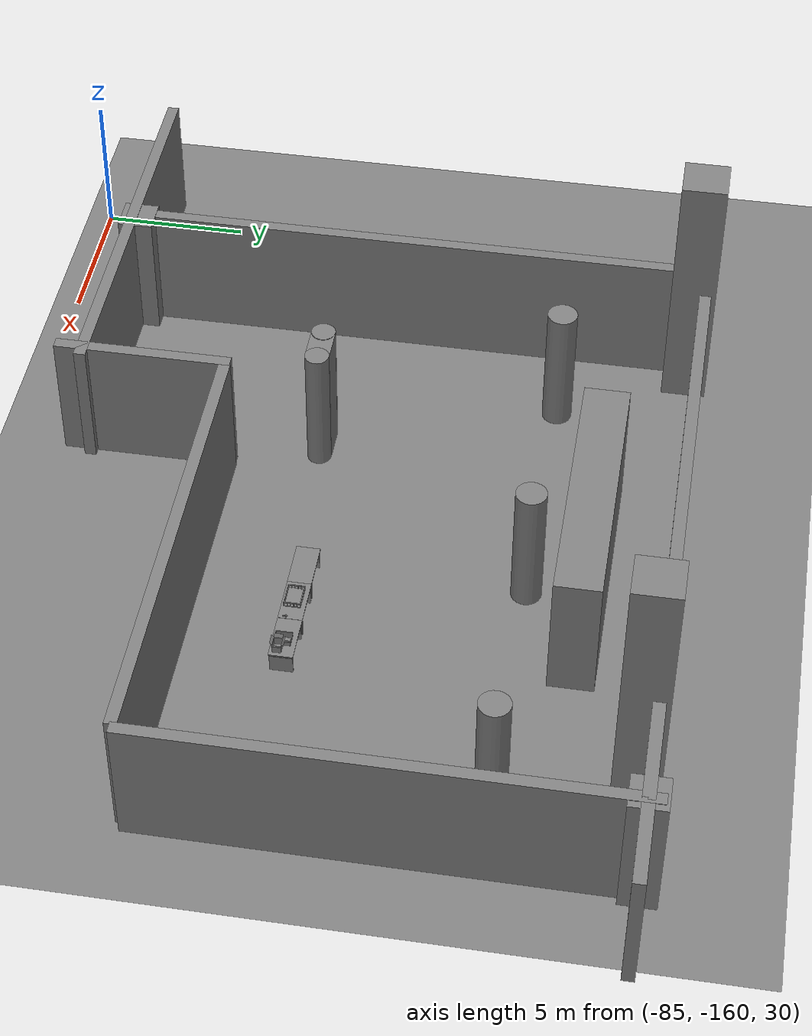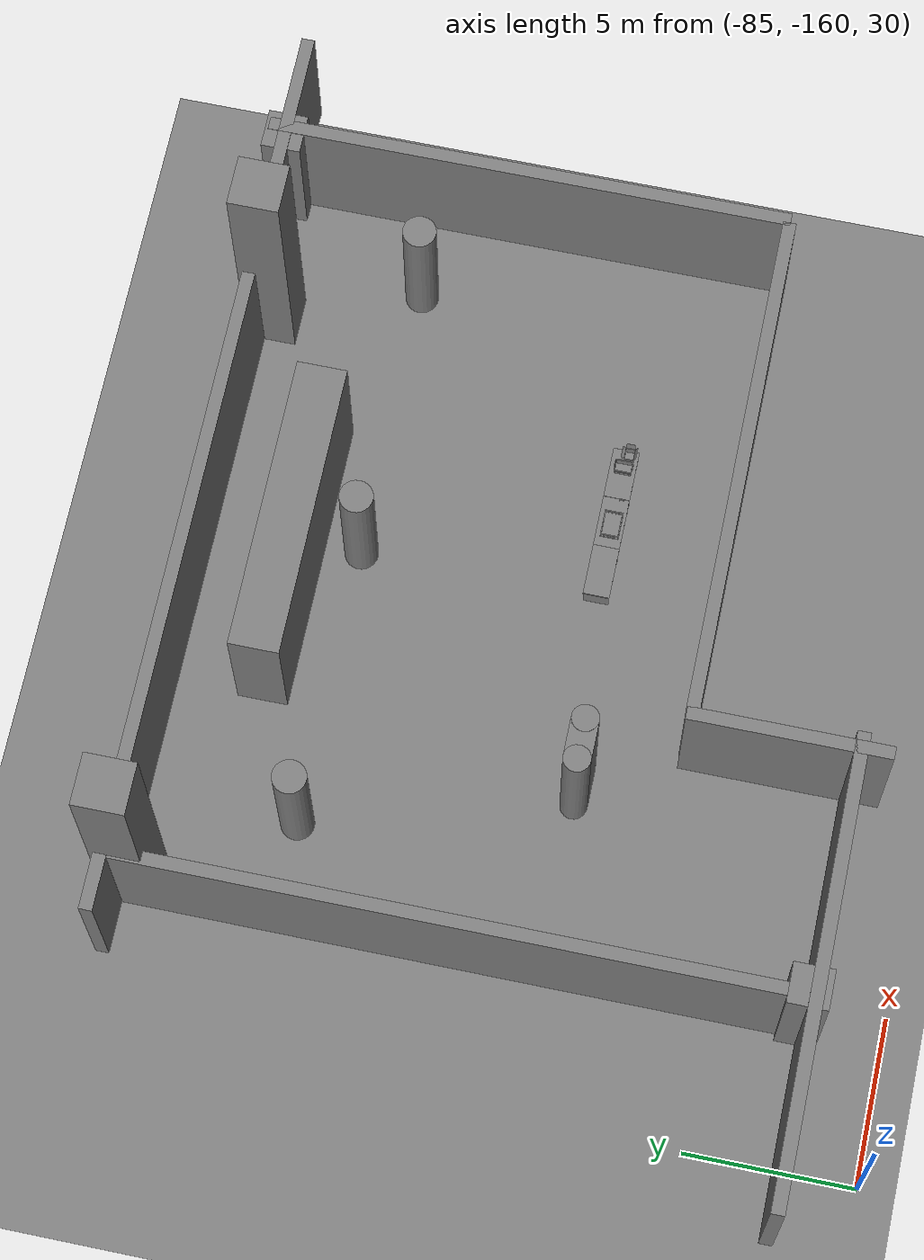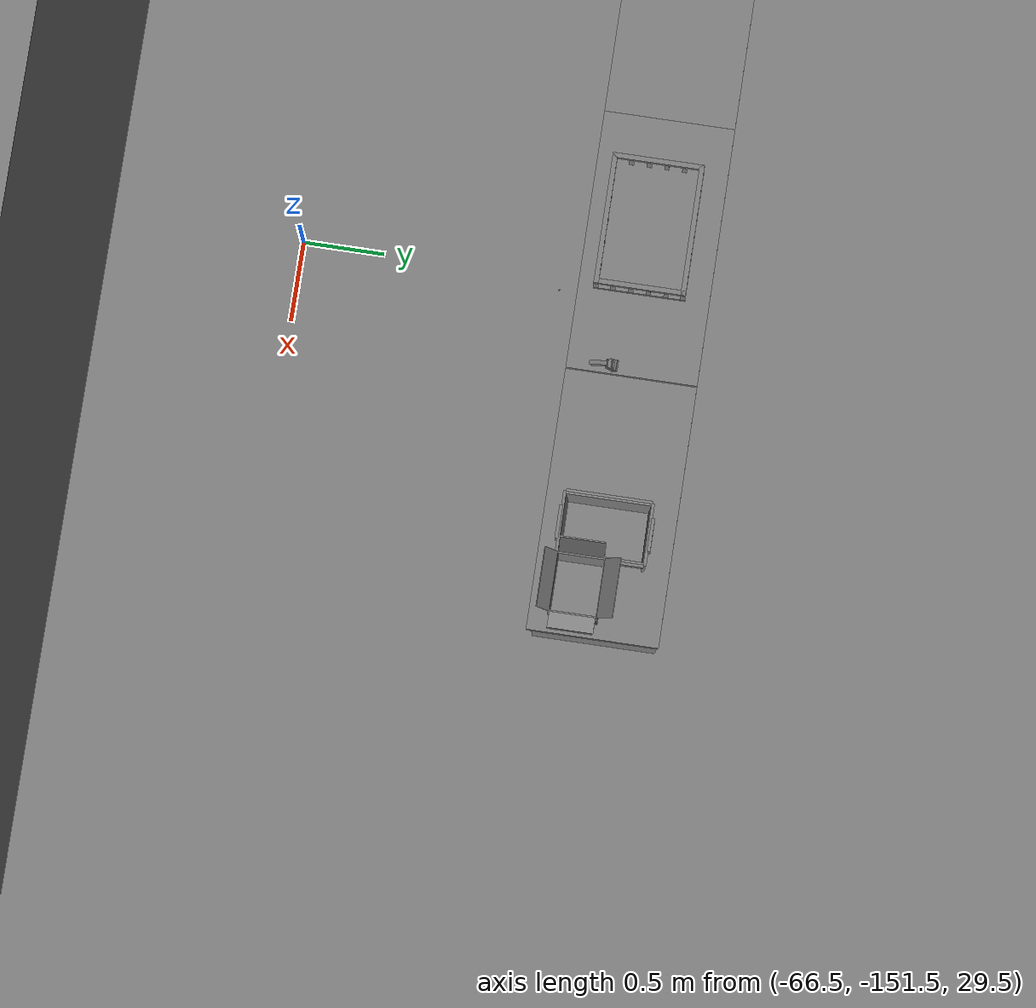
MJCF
<mujoco>
    <option gravity="0.000000000 0.000000000 -9.810000420" timestep="0.0049999999" integrator="implicitfast" density="1.225" viscosity="1.8000001e-05" noslip_iterations="10" iterations="100" sdf_iterations="50">
        <flag multiccd="disable"/>
    </option>
    <size memory="1000M"/>
    <compiler coordinate="local"/>
    <worldbody>
        <light cutoff="30" pos="0 1 1" dir="0 -1 -2"/>
        <light cutoff="30" pos="0 -1 1" dir="0 1 -2"/>
        <body pos="-64.866622925 -149.383972168 30.183746338" euler="89.999992371 89.999946594 0.000000000" name="openloong_gripper_2f85_fix_base_usda_bluebox_01">
            <geom contype="1" conaffinity="1" density="1000" type="box" material="" rgba="0.500000000 0.500000000 0.500000000 1.000000000" solimp="0.899999976 0.949999988 0.001000000" friction="1.000000000 0.005000000 0.000100000" solref="0.020000000 1.000000000" margin="0" condim="3" group="0" pos="0.276596069 0.187225342 0.000061035" quat="0.707107008 0.000077501 0.707106471 0.000077456" size="0.100000001 0.057999998 0.010000000" name="openloong_gripper_2f85_fix_base_usda_geom_4731D899_6B7C_4942_9590_6A3EC7BE87A8"/>
            <geom contype="1" conaffinity="1" density="1000" type="box" material="" rgba="0.500000000 0.500000000 0.500000000 1.000000000" solimp="0.899999976 0.949999988 0.001000000" friction="1.000000000 0.005000000 0.000100000" solref="0.020000000 1.000000000" margin="0" condim="3" group="0" pos="0.000000000 0.002883911 0.000000000" quat="1.000000000 0.000000000 0.000000000 0.000000000" size="0.254000008 0.003000000 0.172000006" name="openloong_gripper_2f85_fix_base_usda_geom_525221A2_488B_472B_82F1_49CF05FE1FF0"/>
            <geom contype="1" conaffinity="1" density="1000" type="box" material="" rgba="0.500000000 0.500000000 0.500000000 1.000000000" solimp="0.899999976 0.949999988 0.001000000" friction="1.000000000 0.005000000 0.000100000" solref="0.020000000 1.000000000" margin="0" condim="3" group="0" pos="0.000015259 0.124874115 0.173477173" quat="0.999796450 0.020176515 -0.000000015 0.000000030" size="0.259999990 0.119999997 0.007000000" name="openloong_gripper_2f85_fix_base_usda_geom_9A16AE8A_7FD2_4354_867B_D00E78848D12"/>
            <geom contype="1" conaffinity="1" density="1000" type="box" material="" rgba="0.500000000 0.500000000 0.500000000 1.000000000" solimp="0.899999976 0.949999988 0.001000000" friction="1.000000000 0.005000000 0.000100000" solref="0.020000000 1.000000000" margin="0" condim="3" group="0" pos="0.000015259 0.124874115 -0.173477173" quat="0.999796450 -0.020176545 -0.000000015 0.000000000" size="0.259999990 0.119999997 0.007000000" name="openloong_gripper_2f85_fix_base_usda_geom_8D35B74D_B4AC_46CB_A436_D8E1263B1839"/>
            <geom contype="1" conaffinity="1" density="1000" type="box" material="" rgba="0.500000000 0.500000000 0.500000000 1.000000000" solimp="0.899999976 0.949999988 0.001000000" friction="1.000000000 0.005000000 0.000100000" solref="0.020000000 1.000000000" margin="0" condim="3" group="0" pos="0.000015259 0.214012146 0.188980103" quat="0.999913096 0.013176724 0.000000015 0.000000000" size="0.259999990 0.029999999 0.012500000" name="openloong_gripper_2f85_fix_base_usda_geom_3D0D719D_80FC_4912_9EC7_C2D5A5321B9B"/>
            <geom contype="1" conaffinity="1" density="1000" type="box" material="" rgba="0.500000000 0.500000000 0.500000000 1.000000000" solimp="0.899999976 0.949999988 0.001000000" friction="1.000000000 0.005000000 0.000100000" solref="0.020000000 1.000000000" margin="0" condim="3" group="0" pos="-0.258346558 0.125289917 0.001876831" quat="0.702796996 -0.020792052 0.710783184 0.020769238" size="0.189999998 0.119999997 0.009000000" name="openloong_gripper_2f85_fix_base_usda_geom_0DCA385F_AA9D_4B89_BB23_134D1C0E7A2A"/>
            <geom contype="1" conaffinity="1" density="1000" type="box" material="" rgba="0.500000000 0.500000000 0.500000000 1.000000000" solimp="0.899999976 0.949999988 0.001000000" friction="1.000000000 0.005000000 0.000100000" solref="0.020000000 1.000000000" margin="0" condim="3" group="0" pos="0.000015259 0.214012146 -0.188980103" quat="0.999913096 -0.013176769 0.000000030 0.000000015" size="0.259999990 0.029999999 0.012500000" name="openloong_gripper_2f85_fix_base_usda_geom_E0658B40_3414_4BC9_8138_DEA06915C89F"/>
            <geom contype="1" conaffinity="1" density="1000" type="box" material="" rgba="0.500000000 0.500000000 0.500000000 1.000000000" solimp="0.899999976 0.949999988 0.001000000" friction="1.000000000 0.005000000 0.000100000" solref="0.020000000 1.000000000" margin="0" condim="3" group="0" pos="-0.276596069 0.187225342 0.000061035" quat="0.707106650 0.000077441 0.707106709 0.000077456" size="0.100000001 0.057999998 0.010000000" name="openloong_gripper_2f85_fix_base_usda_geom_17380C33_CD8F_4869_9C82_DF171723B753"/>
            <geom contype="1" conaffinity="1" density="1000" type="box" material="" rgba="0.500000000 0.500000000 0.500000000 1.000000000" solimp="0.899999976 0.949999988 0.001000000" friction="1.000000000 0.005000000 0.000100000" solref="0.020000000 1.000000000" margin="0" condim="3" group="0" pos="0.258346558 0.125289917 0.001876831" quat="0.702851534 0.018856451 0.710823834 -0.019329429" size="0.189999998 0.119999997 0.009000000" name="openloong_gripper_2f85_fix_base_usda_geom_F54D4750_F431_449D_A471_8CDAB03B1081"/>
            <freejoint name="openloong_gripper_2f85_fix_base_usda_bluebox_01_joint"/>
            <site size="0.005000000 0.005000000 0.005000000" rgba="0.500000000 0.500000000 0.500000000 1.000000000" pos="0.000000000 0.000000000 0.000000000" quat="0.999961913 0.008726534 0.000000000 0.000000000" group="0" type="sphere" name="openloong_gripper_2f85_fix_base_usda_bluebox_01site"/>
        </body>
        <body pos="-64.496299744 -149.491867065 30.235729218" euler="0.000000000 0.000000000 89.999946594" name="openloong_gripper_2f85_fix_base_usda_cardboardbox_01">
            <geom contype="1" conaffinity="1" density="1000" type="box" material="" rgba="0.500000000 0.500000000 0.500000000 1.000000000" solimp="0.899999976 0.949999988 0.001000000" friction="1.000000000 0.005000000 0.000100000" solref="0.020000000 1.000000000" margin="0" condim="3" group="0" pos="-0.003166199 -0.004086494 0.005052090" quat="1.000000000 0.000000000 0.000000000 0.000000000" size="0.142499998 0.177500010 0.005000000" name="openloong_gripper_2f85_fix_base_usda_geom_AC9B77E0_8A89_40D5_8633_954D13B595D8"/>
            <geom contype="1" conaffinity="1" density="1000" type="box" material="" rgba="0.500000000 0.500000000 0.500000000 1.000000000" solimp="0.899999976 0.949999988 0.001000000" friction="1.000000000 0.005000000 0.000100000" solref="0.020000000 1.000000000" margin="0" condim="3" group="0" pos="-0.003166199 0.170316696 0.150570869" quat="1.000000000 0.000000000 0.000000000 0.000000000" size="0.142499998 0.005000000 0.149999991" name="openloong_gripper_2f85_fix_base_usda_geom_4BB3865D_F4F6_4051_8A5A_DF03D5D555C3"/>
            <geom contype="1" conaffinity="1" density="1000" type="box" material="" rgba="0.500000000 0.500000000 0.500000000 1.000000000" solimp="0.899999976 0.949999988 0.001000000" friction="1.000000000 0.005000000 0.000100000" solref="0.020000000 1.000000000" margin="0" condim="3" group="0" pos="-0.147399902 -0.005307198 0.150570869" quat="1.000000000 0.000000000 0.000000000 0.000000000" size="0.005000000 0.177500010 0.149999991" name="openloong_gripper_2f85_fix_base_usda_geom_CC4981A5_A0BC_4C5C_848D_B050EF439365"/>
            <geom contype="1" conaffinity="1" density="1000" type="box" material="" rgba="0.500000000 0.500000000 0.500000000 1.000000000" solimp="0.899999976 0.949999988 0.001000000" friction="1.000000000 0.005000000 0.000100000" solref="0.020000000 1.000000000" margin="0" condim="3" group="0" pos="0.140275955 -0.005307198 0.150570869" quat="1.000000000 0.000000000 0.000000000 0.000000000" size="0.005000000 0.177500010 0.149999991" name="openloong_gripper_2f85_fix_base_usda_geom_6A70CAF3_DA78_4ED6_98C4_0EB92B0CEB7E"/>
            <geom contype="1" conaffinity="1" density="1000" type="box" material="" rgba="0.500000000 0.500000000 0.500000000 1.000000000" solimp="0.899999976 0.949999988 0.001000000" friction="1.000000000 0.005000000 0.000100000" solref="0.020000000 1.000000000" margin="0" condim="3" group="0" pos="-0.003166199 -0.181550980 0.150570869" quat="1.000000000 0.000000000 0.000000000 0.000000000" size="0.142499998 0.005000000 0.149999991" name="openloong_gripper_2f85_fix_base_usda_geom_8B1D4EB9_C621_4E10_9FD4_EB0648AA9859"/>
            <freejoint name="openloong_gripper_2f85_fix_base_usda_cardboardbox_01_joint"/>
            <site size="0.005000000 0.005000000 0.005000000" rgba="0.500000000 0.500000000 0.500000000 1.000000000" pos="0.000000000 0.000000000 0.000000000" quat="0.999961913 0.008726535 0.000000000 0.000000000" group="0" type="sphere" name="openloong_gripper_2f85_fix_base_usda_site_1B1D5D6F_A71F_49D0_9A29_D1D6B939514B"/>
            <body pos="0.139160156 -0.004048347 0.301930904" euler="-179.999954224 49.383502960 179.999954224" name="openloong_gripper_2f85_fix_base_usda_A1_006">
                <geom contype="1" conaffinity="1" density="1000" type="box" material="" rgba="0.500000000 0.500000000 0.500000000 1.000000000" solimp="0.899999976 0.949999988 0.001000000" friction="1.000000000 0.005000000 0.000100000" solref="0.020000000 1.000000000" margin="0" condim="3" group="0" pos="-0.071587563 0.000009537 0.001745224" quat="0.999999881 0.000000000 0.000000000 0.000000000" size="0.071249999 0.179999992 0.002500000" name="openloong_gripper_2f85_fix_base_usda_geom_66A75C20_A7C5_4903_B7A0_F67EF4EA3EA6"/>
                <joint armature="0" stiffness="0.07" damping="0.0099999998" axis="0.000000 1.000000 0.000000" type="hinge" name="openloong_gripper_2f85_fix_base_usda_A1_006"/>
            </body>
            <body pos="-0.145902634 -0.004086494 0.301938057" euler="-180.000000000 -60.000011444 -180.000000000" name="openloong_gripper_2f85_fix_base_usda_A2_006">
                <geom contype="1" conaffinity="1" density="1000" type="box" material="" rgba="0.500000000 0.500000000 0.500000000 1.000000000" solimp="0.899999976 0.949999988 0.001000000" friction="1.000000000 0.005000000 0.000100000" solref="0.020000000 1.000000000" margin="0" condim="3" group="0" pos="0.071268082 0.000009537 0.002717972" quat="0.000002921 0.000000000 -0.000000030 0.999999881" size="0.071249999 0.179999992 0.002500000" name="openloong_gripper_2f85_fix_base_usda_geom_BCC03B35_96C7_4B76_967B_733B525D0715"/>
                <joint armature="0" stiffness="0.07" damping="0.0099999998" axis="0.000000 1.000000 0.000000" type="hinge" name="openloong_gripper_2f85_fix_base_usda_A2_006"/>
            </body>
            <body pos="-0.003385544 0.175991058 0.301930904" euler="-125.858116150 -0.000004561 0.000002331" name="openloong_gripper_2f85_fix_base_usda_B2_006">
                <geom contype="1" conaffinity="1" density="1000" type="box" material="" rgba="0.500000000 0.500000000 0.500000000 1.000000000" solimp="0.899999976 0.949999988 0.001000000" friction="1.000000000 0.005000000 0.000100000" solref="0.020000000 1.000000000" margin="0" condim="3" group="0" pos="0.000009537 -0.070939064 -0.002470016" quat="0.999614120 0.027776197 -0.000000015 0.000000030" size="0.137500003 0.064999998 0.005000000" name="openloong_gripper_2f85_fix_base_usda_geom_2955FF8C_5EFD_47C0_9DEC_39CFFC0D89D3"/>
                <joint armature="0" stiffness="0.07" damping="0.0099999998" axis="1.000000 0.000000 0.000000" type="hinge" name="openloong_gripper_2f85_fix_base_usda_B2_006"/>
            </body>
            <body pos="-0.003385544 -0.184140205 0.301938057" euler="147.805557251 0.000000000 0.000000000" name="openloong_gripper_2f85_fix_base_usda_B1_006">
                <geom contype="1" conaffinity="1" density="1000" type="box" material="" rgba="0.500000000 0.500000000 0.500000000 1.000000000" solimp="0.899999976 0.949999988 0.001000000" friction="1.000000000 0.005000000 0.000100000" solref="0.020000000 1.000000000" margin="0" condim="3" group="0" pos="-0.000028610 0.070202351 -0.002703667" quat="0.999614179 -0.027776167 0.000000000 0.000000000" size="0.137500003 0.064999998 0.005000000" name="openloong_gripper_2f85_fix_base_usda_geom_B4CB1421_9298_493F_85EA_9CAE8CD13FCD"/>
                <joint armature="0" stiffness="0.07" damping="0.0099999998" axis="1.000000 0.000000 0.000000" type="hinge" name="openloong_gripper_2f85_fix_base_usda_B1_006"/>
            </body>
        </body>
        <body pos="-65.882858276 -149.481979370 30.229999542" euler="-64.487716675 0.000000000 0.000000000" name="openloong_gripper_2f85_fix_base_usda_Barcode">
            <geom contype="1" conaffinity="1" density="1000" type="box" material="" rgba="0.500000000 0.500000000 0.500000000 1.000000000" solimp="0.899999976 0.949999988 0.001000000" friction="1.000000000 0.005000000 0.000100000" solref="0.020000000 1.000000000" margin="0" condim="3" group="0" pos="0.000000000 0.013038635 0.001419067" quat="0.000000000 0.000000000 0.000000000 1.000000119" size="0.034000002 0.010000000 0.017999999" name="openloong_gripper_2f85_fix_base_usda_geom_0C81EBE5_B32A_4EA1_8FFF_2F187032C629"/>
            <geom contype="1" conaffinity="1" density="1000" type="box" material="" rgba="0.500000000 0.500000000 0.500000000 1.000000000" solimp="0.899999976 0.949999988 0.001000000" friction="1.000000000 0.005000000 0.000100000" solref="0.020000000 1.000000000" margin="0" condim="3" group="0" pos="0.000000000 -0.035301208 -0.007095337" quat="0.000000000 0.000000000 -0.043619365 0.999048233" size="0.028999999 0.010000000 0.020000000" name="openloong_gripper_2f85_fix_base_usda_geom_1FDA4795_277F_4384_96DF_4A78D2560942"/>
            <geom contype="1" conaffinity="1" density="1000" type="box" material="" rgba="0.500000000 0.500000000 0.500000000 1.000000000" solimp="0.899999976 0.949999988 0.001000000" friction="1.000000000 0.005000000 0.000100000" solref="0.020000000 1.000000000" margin="0" condim="3" group="0" pos="0.000000000 -0.043411255 -0.011749268" quat="0.922262907 0.386563420 0.000000000 0.000000000" size="0.026000001 0.010000000 0.020000000" name="openloong_gripper_2f85_fix_base_usda_geom_0A9E2938_BDE1_4F09_8741_E07203A64D43"/>
            <geom contype="1" conaffinity="1" density="1000" type="box" material="" rgba="0.500000000 0.500000000 0.500000000 1.000000000" solimp="0.899999976 0.949999988 0.001000000" friction="1.000000000 0.005000000 0.000100000" solref="0.020000000 1.000000000" margin="0" condim="3" group="0" pos="0.000000000 -0.016967773 -0.031860352" quat="0.000000000 0.000000000 0.000000000 1.000000119" size="0.008000000 0.010000000 0.013000000" name="openloong_gripper_2f85_fix_base_usda_geom_9DF3D4BD_8908_407F_904B_671C3B80E80F"/>
            <geom contype="1" conaffinity="1" density="1000" type="box" material="" rgba="0.500000000 0.500000000 0.500000000 1.000000000" solimp="0.899999976 0.949999988 0.001000000" friction="1.000000000 0.005000000 0.000100000" solref="0.020000000 1.000000000" margin="0" condim="3" group="0" pos="0.000000000 -0.001869202 0.000312805" quat="0.953716993 0.300705761 0.000000000 0.000000000" size="0.032000002 0.010000000 0.018999999" name="openloong_gripper_2f85_fix_base_usda_geom_FAED5E3B_863C_4AF5_A704_99D80A709CEC"/>
            <geom contype="1" conaffinity="1" density="1000" type="box" material="" rgba="0.500000000 0.500000000 0.500000000 1.000000000" solimp="0.899999976 0.949999988 0.001000000" friction="1.000000000 0.005000000 0.000100000" solref="0.020000000 1.000000000" margin="0" condim="3" group="0" pos="0.000000000 -0.019531250 -0.003173828" quat="0.953716993 0.300705761 0.000000000 0.000000000" size="0.030999999 0.010000000 0.020000000" name="openloong_gripper_2f85_fix_base_usda_geom_EFE8F02F_7FB3_4F38_9F08_688A3210BC3F"/>
            <geom contype="1" conaffinity="1" density="1000" type="box" material="" rgba="0.500000000 0.500000000 0.500000000 1.000000000" solimp="0.899999976 0.949999988 0.001000000" friction="1.000000000 0.005000000 0.000100000" solref="0.020000000 1.000000000" margin="0" condim="3" group="0" pos="0.000000000 -0.035301208 -0.007095337" quat="0.953716993 0.300705761 0.000000000 0.000000000" size="0.028999999 0.010000000 0.020000000" name="openloong_gripper_2f85_fix_base_usda_geom_ADD71CCF_4022_4A2D_8891_6BA2AF6642E8"/>
            <geom contype="1" conaffinity="1" density="1000" type="box" material="" rgba="0.500000000 0.500000000 0.500000000 1.000000000" solimp="0.899999976 0.949999988 0.001000000" friction="1.000000000 0.005000000 0.000100000" solref="0.020000000 1.000000000" margin="0" condim="3" group="0" pos="0.000000000 -0.042617798 -0.071121216" quat="0.000000000 0.000000000 0.000000000 1.000000119" size="0.013000000 0.021000000 0.059999999" name="openloong_gripper_2f85_fix_base_usda_geom_5D79956E_9404_4534_8E3A_0D49A1563CBC"/>
            <freejoint name="openloong_gripper_2f85_fix_base_usda_Barcode_joint"/>
            <site size="0.005000000 0.005000000 0.005000000" rgba="0.500000000 0.500000000 0.500000000 1.000000000" pos="0.000000000 0.000000000 0.000000000" quat="1.000000000 0.000000000 0.000000000 0.000000000" group="0" type="sphere" name="openloong_gripper_2f85_fix_base_usda_Barcode_site"/>
        </body>
        <body pos="-66.745018005 -149.392349243 30.184000015" euler="0.000000000 0.000000000 89.999946594" name="[22329835471394]_Basket_01">
            <geom contype="1" conaffinity="1" density="1000" type="box" material="" rgba="0.500000000 0.500000000 0.500000000 1.000000000" solimp="0.899999976 0.949999988 0.001000000" friction="1.000000000 0.005000000 0.000100000" solref="0.020000000 1.000000000" margin="0" condim="3" group="0" pos="-0.052425385 0.389207840 0.089787483" quat="0.707107008 0.000000000 0.000000000 0.707106411" size="0.014249999 0.014249999 0.059999999" name="[22329835471394]_geom_2E16C86E_BCD1_433C_ABCB_050A268F8B77"/>
            <geom contype="1" conaffinity="1" density="1000" type="box" material="" rgba="0.500000000 0.500000000 0.500000000 1.000000000" solimp="0.899999976 0.949999988 0.001000000" friction="1.000000000 0.005000000 0.000100000" solref="0.020000000 1.000000000" margin="0" condim="3" group="0" pos="0.264015198 -0.133043289 0.089787483" quat="0.707107008 0.000000000 0.000000000 0.707106411" size="0.014249999 0.014249999 0.059999999" name="[22329835471394]_geom_30F09776_0407_43D0_A5E3_5F484D552582"/>
            <geom contype="1" conaffinity="1" density="1000" type="box" material="" rgba="0.500000000 0.500000000 0.500000000 1.000000000" solimp="0.899999976 0.949999988 0.001000000" friction="1.000000000 0.005000000 0.000100000" solref="0.020000000 1.000000000" margin="0" condim="3" group="0" pos="-0.264015198 -0.265548706 0.089793205" quat="0.707107008 0.000000000 0.000000000 0.707106411" size="0.014249999 0.014249999 0.059999999" name="[22329835471394]_geom_61B135DD_7B8D_49A2_B39F_72315BB5E087"/>
            <geom contype="1" conaffinity="1" density="1000" type="box" material="" rgba="0.500000000 0.500000000 0.500000000 1.000000000" solimp="0.899999976 0.949999988 0.001000000" friction="1.000000000 0.005000000 0.000100000" solref="0.020000000 1.000000000" margin="0" condim="3" group="0" pos="-0.160263062 -0.389322281 0.089793205" quat="0.707107008 0.000000000 0.000000000 0.707106411" size="0.014249999 0.014249999 0.059999999" name="[22329835471394]_geom_C97674E0_D183_4FF4_937F_5C316C9A1E2D"/>
            <geom contype="1" conaffinity="1" density="1000" type="box" material="" rgba="0.500000000 0.500000000 0.500000000 1.000000000" solimp="0.899999976 0.949999988 0.001000000" friction="1.000000000 0.005000000 0.000100000" solref="0.020000000 1.000000000" margin="0" condim="3" group="0" pos="0.162265778 -0.389322281 0.089787483" quat="0.707107008 0.000000000 0.000000000 0.707106411" size="0.014249999 0.014249999 0.059999999" name="[22329835471394]_geom_94483837_CE83_4175_BA39_DB6471FC8C7D"/>
            <geom contype="1" conaffinity="1" density="1000" type="box" material="" rgba="0.500000000 0.500000000 0.500000000 1.000000000" solimp="0.899999976 0.949999988 0.001000000" friction="1.000000000 0.005000000 0.000100000" solref="0.020000000 1.000000000" margin="0" condim="3" group="0" pos="0.264015198 0.389207840 0.089787483" quat="0.707107008 0.000000000 0.000000000 0.707106411" size="0.014249999 0.014249999 0.059999999" name="[22329835471394]_geom_0314C210_7411_4E60_9FF8_366F0A33BE5B"/>
            <geom contype="1" conaffinity="1" density="1000" type="box" material="" rgba="0.500000000 0.500000000 0.500000000 1.000000000" solimp="0.899999976 0.949999988 0.001000000" friction="1.000000000 0.005000000 0.000100000" solref="0.020000000 1.000000000" margin="0" condim="3" group="0" pos="-0.264015198 -0.133043289 0.089793205" quat="0.707107008 0.000000000 0.000000000 0.707106411" size="0.014249999 0.014249999 0.059999999" name="[22329835471394]_geom_A2361F19_FC82_4FB5_BB6E_3F54787A7FAB"/>
            <geom contype="1" conaffinity="1" density="1000" type="box" material="" rgba="0.500000000 0.500000000 0.500000000 1.000000000" solimp="0.899999976 0.949999988 0.001000000" friction="1.000000000 0.005000000 0.000100000" solref="0.020000000 1.000000000" margin="0" condim="3" group="0" pos="-0.264026642 0.269256592 0.089793205" quat="0.707107008 0.000000000 0.000000000 0.707106411" size="0.014249999 0.014249999 0.059999999" name="[22329835471394]_geom_2188999D_D14B_416D_8EF6_07112E67BD5C"/>
            <geom contype="1" conaffinity="1" density="1000" type="box" material="" rgba="0.500000000 0.500000000 0.500000000 1.000000000" solimp="0.899999976 0.949999988 0.001000000" friction="1.000000000 0.005000000 0.000100000" solref="0.020000000 1.000000000" margin="0" condim="3" group="0" pos="0.054462433 0.389207840 0.089787483" quat="0.707107008 0.000000000 0.000000000 0.707106411" size="0.014249999 0.014249999 0.059999999" name="[22329835471394]_geom_79C4B9B7_A324_470A_BFC6_C953154F0752"/>
            <geom contype="1" conaffinity="1" density="1000" type="box" material="" rgba="0.500000000 0.500000000 0.500000000 1.000000000" solimp="0.899999976 0.949999988 0.001000000" friction="1.000000000 0.005000000 0.000100000" solref="0.020000000 1.000000000" margin="0" condim="3" group="0" pos="0.054462433 -0.389322281 0.089787483" quat="0.707107008 0.000000000 0.000000000 0.707106411" size="0.014249999 0.014249999 0.059999999" name="[22329835471394]_geom_544838F9_5EB1_49C4_845E_867A3276A098"/>
            <geom contype="1" conaffinity="1" density="1000" type="box" material="" rgba="0.500000000 0.500000000 0.500000000 1.000000000" solimp="0.899999976 0.949999988 0.001000000" friction="1.000000000 0.005000000 0.000100000" solref="0.020000000 1.000000000" margin="0" condim="3" group="0" pos="0.264015198 0.269256592 0.089793205" quat="0.707107008 0.000000000 0.000000000 0.707106411" size="0.014249999 0.014249999 0.059999999" name="[22329835471394]_geom_7CFBF41F_DFDA_44D9_8D40_2E146363E180"/>
            <geom contype="1" conaffinity="1" density="1000" type="box" material="" rgba="0.500000000 0.500000000 0.500000000 1.000000000" solimp="0.899999976 0.949999988 0.001000000" friction="1.000000000 0.005000000 0.000100000" solref="0.020000000 1.000000000" margin="0" condim="3" group="0" pos="0.264015198 -0.389322281 0.089787483" quat="0.707107008 0.000000000 0.000000000 0.707106411" size="0.014249999 0.014249999 0.059999999" name="[22329835471394]_geom_94E9D17D_3584_4836_808A_554516B2F554"/>
            <geom contype="1" conaffinity="1" density="1000" type="box" material="" rgba="0.500000000 0.500000000 0.500000000 1.000000000" solimp="0.899999976 0.949999988 0.001000000" friction="1.000000000 0.005000000 0.000100000" solref="0.020000000 1.000000000" margin="0" condim="3" group="0" pos="0.000000000 0.000000000 0.015998840" quat="0.707107008 0.000000000 0.000000000 0.707106411" size="0.403499991 0.279000014 0.015750000" name="[22329835471394]_geom_C5A6298B_2DC2_48A9_91AC_84D5B0959322"/>
            <geom contype="1" conaffinity="1" density="1000" type="box" material="" rgba="0.500000000 0.500000000 0.500000000 1.000000000" solimp="0.899999976 0.949999988 0.001000000" friction="1.000000000 0.005000000 0.000100000" solref="0.020000000 1.000000000" margin="0" condim="3" group="0" pos="0.000000000 -0.389476776 0.163619041" quat="0.707107008 0.000000000 0.000000000 0.707106411" size="0.015000000 0.277500004 0.015750000" name="[22329835471394]_geom_F8DAA380_9CC5_49B4_8557_2906628ABAA7"/>
            <geom contype="1" conaffinity="1" density="1000" type="box" material="" rgba="0.500000000 0.500000000 0.500000000 1.000000000" solimp="0.899999976 0.949999988 0.001000000" friction="1.000000000 0.005000000 0.000100000" solref="0.020000000 1.000000000" margin="0" condim="3" group="0" pos="0.162265778 0.389207840 0.089787483" quat="0.707107008 0.000000000 0.000000000 0.707106411" size="0.014249999 0.014249999 0.059999999" name="[22329835471394]_geom_BF9F41B7_EDDF_44E7_AB10_D3AE7C584081"/>
            <geom contype="1" conaffinity="1" density="1000" type="box" material="" rgba="0.500000000 0.500000000 0.500000000 1.000000000" solimp="0.899999976 0.949999988 0.001000000" friction="1.000000000 0.005000000 0.000100000" solref="0.020000000 1.000000000" margin="0" condim="3" group="0" pos="0.000000000 0.389471054 0.163619041" quat="0.707107008 0.000000000 0.000000000 0.707106411" size="0.015000000 0.277500004 0.015750000" name="[22329835471394]_geom_6327FD9B_DF99_4D15_9A06_5C85125FAC88"/>
            <geom contype="1" conaffinity="1" density="1000" type="box" material="" rgba="0.500000000 0.500000000 0.500000000 1.000000000" solimp="0.899999976 0.949999988 0.001000000" friction="1.000000000 0.005000000 0.000100000" solref="0.020000000 1.000000000" margin="0" condim="3" group="0" pos="-0.263511658 0.000000000 0.163619041" quat="0.707107008 0.000000000 0.000000000 0.707106411" size="0.403499991 0.015000000 0.015750000" name="[22329835471394]_geom_5656F6D6_8559_47DA_8477_756F993A50BD"/>
            <geom contype="1" conaffinity="1" density="1000" type="box" material="" rgba="0.500000000 0.500000000 0.500000000 1.000000000" solimp="0.899999976 0.949999988 0.001000000" friction="1.000000000 0.005000000 0.000100000" solref="0.020000000 1.000000000" margin="0" condim="3" group="0" pos="-0.264015198 0.141334534 0.089793205" quat="0.707107008 0.000000000 0.000000000 0.707106411" size="0.014249999 0.014249999 0.059999999" name="[22329835471394]_geom_59979EAB_67DA_49B9_B928_0A667529AE23"/>
            <geom contype="1" conaffinity="1" density="1000" type="box" material="" rgba="0.500000000 0.500000000 0.500000000 1.000000000" solimp="0.899999976 0.949999988 0.001000000" friction="1.000000000 0.005000000 0.000100000" solref="0.020000000 1.000000000" margin="0" condim="3" group="0" pos="0.264015198 -0.265548706 0.089787483" quat="0.707107008 0.000000000 0.000000000 0.707106411" size="0.014249999 0.014249999 0.059999999" name="[22329835471394]_geom_E54AAC63_3ACE_480E_874E_82BC6B937E47"/>
            <geom contype="1" conaffinity="1" density="1000" type="box" material="" rgba="0.500000000 0.500000000 0.500000000 1.000000000" solimp="0.899999976 0.949999988 0.001000000" friction="1.000000000 0.005000000 0.000100000" solref="0.020000000 1.000000000" margin="0" condim="3" group="0" pos="-0.160263062 0.389207840 0.089787483" quat="0.707107008 0.000000000 0.000000000 0.707106411" size="0.014249999 0.014249999 0.059999999" name="[22329835471394]_geom_1D92F55F_9123_499D_9AF9_30A5AE2DB311"/>
            <geom contype="1" conaffinity="1" density="1000" type="box" material="" rgba="0.500000000 0.500000000 0.500000000 1.000000000" solimp="0.899999976 0.949999988 0.001000000" friction="1.000000000 0.005000000 0.000100000" solref="0.020000000 1.000000000" margin="0" condim="3" group="0" pos="-0.052425385 -0.389322281 0.089787483" quat="0.707107008 0.000000000 0.000000000 0.707106411" size="0.014249999 0.014249999 0.059999999" name="[22329835471394]_geom_185F26C1_A518_411D_8DC1_9AFD0EB20944"/>
            <geom contype="1" conaffinity="1" density="1000" type="box" material="" rgba="0.500000000 0.500000000 0.500000000 1.000000000" solimp="0.899999976 0.949999988 0.001000000" friction="1.000000000 0.005000000 0.000100000" solref="0.020000000 1.000000000" margin="0" condim="3" group="0" pos="-0.264026642 -0.389322281 0.089793205" quat="0.707107008 0.000000000 0.000000000 0.707106411" size="0.014249999 0.014249999 0.059999999" name="[22329835471394]_geom_FFA1B219_C842_4572_AC5B_500F0BBE265B"/>
            <geom contype="1" conaffinity="1" density="1000" type="box" material="" rgba="0.500000000 0.500000000 0.500000000 1.000000000" solimp="0.899999976 0.949999988 0.001000000" friction="1.000000000 0.005000000 0.000100000" solref="0.020000000 1.000000000" margin="0" condim="3" group="0" pos="0.264015198 0.141334534 0.089787483" quat="0.707107008 0.000000000 0.000000000 0.707106411" size="0.014249999 0.014249999 0.059999999" name="[22329835471394]_geom_42B646A4_15FD_4703_8275_AA8186CF6FCD"/>
            <geom contype="1" conaffinity="1" density="1000" type="box" material="" rgba="0.500000000 0.500000000 0.500000000 1.000000000" solimp="0.899999976 0.949999988 0.001000000" friction="1.000000000 0.005000000 0.000100000" solref="0.020000000 1.000000000" margin="0" condim="3" group="0" pos="-0.264015198 0.389207840 0.089793205" quat="0.707107008 0.000000000 0.000000000 0.707106411" size="0.014249999 0.014249999 0.059999999" name="[22329835471394]_geom_801D952C_52F3_406E_9289_ED2780426E86"/>
            <geom contype="1" conaffinity="1" density="1000" type="box" material="" rgba="0.500000000 0.500000000 0.500000000 1.000000000" solimp="0.899999976 0.949999988 0.001000000" friction="1.000000000 0.005000000 0.000100000" solref="0.020000000 1.000000000" margin="0" condim="3" group="0" pos="0.264015198 0.004480362 0.089787483" quat="0.707107008 0.000000000 0.000000000 0.707106411" size="0.014249999 0.014249999 0.059999999" name="[22329835471394]_geom_B370B541_09D4_464A_87C4_A2AB5FA657E8"/>
            <geom contype="1" conaffinity="1" density="1000" type="box" material="" rgba="0.500000000 0.500000000 0.500000000 1.000000000" solimp="0.899999976 0.949999988 0.001000000" friction="1.000000000 0.005000000 0.000100000" solref="0.020000000 1.000000000" margin="0" condim="3" group="0" pos="0.263694763 -0.000011444 0.163619041" quat="0.707107008 0.000000000 0.000000000 0.707106411" size="0.403499991 0.015000000 0.015750000" name="[22329835471394]_geom_D7F4BCE1_54EA_45B8_BB75_951E627B8C66"/>
            <geom contype="1" conaffinity="1" density="1000" type="box" material="" rgba="0.500000000 0.500000000 0.500000000 1.000000000" solimp="0.899999976 0.949999988 0.001000000" friction="1.000000000 0.005000000 0.000100000" solref="0.020000000 1.000000000" margin="0" condim="3" group="0" pos="-0.264015198 0.004480362 0.089793205" quat="0.707107008 0.000000000 0.000000000 0.707106411" size="0.014249999 0.014249999 0.059999999" name="[22329835471394]_geom_30F6A451_3D69_445A_8963_9C685E9FAC5D"/>
            <freejoint name="[22329835471394]_joint_0274F65F_CE16_4F98_A853_044E18F6A295"/>
        </body>
        <body pos="0.000000000 0.000000000 0.000000000" euler="0.000000000 0.000000000 0.000000000" name="Static Objects_Static Objects">
            <geom contype="1" conaffinity="1" density="1000" type="box" material="" rgba="0.500000000 0.500000000 0.500000000 1.000000000" solimp="0.899999976 0.949999988 0.001000000" friction="1.000000000 0.005000000 0.000100000" solref="0.020000000 1.000000000" margin="0" condim="3" group="0" pos="-67.544113159 -149.365814209 29.727830887" quat="0.500000417 0.499999970 0.499999553 0.499999970" size="0.381000012 0.319999993 0.041000001" name="Static Objects_geom_17A591AF_3B72_4116_999B_E22F2A293C71"/>
            <geom contype="1" conaffinity="1" density="1000" type="box" material="" rgba="0.500000000 0.500000000 0.500000000 1.000000000" solimp="0.899999976 0.949999988 0.001000000" friction="1.000000000 0.005000000 0.000100000" solref="0.020000000 1.000000000" margin="0" condim="3" group="0" pos="-68.239501953 -149.365814209 30.086868286" quat="0.500000417 0.499999970 0.499999553 0.499999970" size="0.370999992 0.039500002 0.745000005" name="Static Objects_geom_B66199FB_943A_4C20_8BA7_0DF94C117B82"/>
            <geom contype="1" conaffinity="1" density="1000" type="box" material="" rgba="0.500000000 0.500000000 0.500000000 1.000000000" solimp="0.899999976 0.949999988 0.001000000" friction="1.000000000 0.005000000 0.000100000" solref="0.020000000 1.000000000" margin="0" condim="3" group="0" pos="-68.239501953 -149.365814209 30.147235870" quat="0.500000417 0.499999970 0.499999553 0.499999970" size="0.400000006 0.022000000 0.800000012" name="Static Objects_geom_88D2EA78_FD77_4536_B79D_E041BB176F50"/>
            <geom contype="1" conaffinity="1" density="1000" type="box" material="" rgba="0.500000000 0.500000000 0.500000000 1.000000000" solimp="0.899999976 0.949999988 0.001000000" friction="1.000000000 0.005000000 0.000100000" solref="0.020000000 1.000000000" margin="0" condim="3" group="0" pos="-68.934890747 -149.365814209 29.727830887" quat="0.500000417 0.499999970 0.499999553 0.499999970" size="0.381000012 0.319999993 0.041000001" name="Static Objects_geom_B2D52EEA_4522_464B_8088_F8680E3B0A33"/>
            <geom contype="1" conaffinity="1" density="1000" type="box" material="" rgba="0.500000000 0.500000000 0.500000000 1.000000000" solimp="0.899999976 0.949999988 0.001000000" friction="1.000000000 0.005000000 0.000100000" solref="0.020000000 1.000000000" margin="0" condim="3" group="0" pos="-68.239501953 -149.365814209 29.561563492" quat="0.500000417 0.499999970 0.499999553 0.499999970" size="0.020000000 0.022000000 0.660000026" name="Static Objects_geom_7FFCB350_9FC2_4BA8_89A2_8CC3A517469D"/>
            <geom contype="1" conaffinity="1" density="1000" type="box" material="" rgba="0.500000000 0.500000000 0.500000000 1.000000000" solimp="0.899999976 0.949999988 0.001000000" friction="1.000000000 0.005000000 0.000100000" solref="0.020000000 1.000000000" margin="0" condim="3" group="0" pos="-65.945671082 -149.365814209 29.727830887" quat="0.500000417 0.499999970 0.499999553 0.499999970" size="0.381000012 0.319999993 0.041000001" name="Static Objects_geom_81B87014_B34F_4398_AB41_2E64119B07BB"/>
            <geom contype="1" conaffinity="1" density="1000" type="box" material="" rgba="0.500000000 0.500000000 0.500000000 1.000000000" solimp="0.899999976 0.949999988 0.001000000" friction="1.000000000 0.005000000 0.000100000" solref="0.020000000 1.000000000" margin="0" condim="3" group="0" pos="-66.641059875 -149.365814209 30.086868286" quat="0.500000417 0.499999970 0.499999553 0.499999970" size="0.370999992 0.039500002 0.745000005" name="Static Objects_geom_ED6A99E8_16CF_4488_A78C_74869B191827"/>
            <geom contype="1" conaffinity="1" density="1000" type="box" material="" rgba="0.500000000 0.500000000 0.500000000 1.000000000" solimp="0.899999976 0.949999988 0.001000000" friction="1.000000000 0.005000000 0.000100000" solref="0.020000000 1.000000000" margin="0" condim="3" group="0" pos="-66.641059875 -149.365814209 30.147235870" quat="0.500000417 0.499999970 0.499999553 0.499999970" size="0.400000006 0.022000000 0.800000012" name="Static Objects_geom_1DCF5AAF_5DDA_4728_88C2_DC306873F3D9"/>
            <geom contype="1" conaffinity="1" density="1000" type="box" material="" rgba="0.500000000 0.500000000 0.500000000 1.000000000" solimp="0.899999976 0.949999988 0.001000000" friction="1.000000000 0.005000000 0.000100000" solref="0.020000000 1.000000000" margin="0" condim="3" group="0" pos="-67.336448669 -149.365814209 29.727830887" quat="0.500000417 0.499999970 0.499999553 0.499999970" size="0.381000012 0.319999993 0.041000001" name="Static Objects_geom_77B139D8_8119_44D1_9150_92E2C40E0767"/>
            <geom contype="1" conaffinity="1" density="1000" type="box" material="" rgba="0.500000000 0.500000000 0.500000000 1.000000000" solimp="0.899999976 0.949999988 0.001000000" friction="1.000000000 0.005000000 0.000100000" solref="0.020000000 1.000000000" margin="0" condim="3" group="0" pos="-66.641059875 -149.365814209 29.561563492" quat="0.500000417 0.499999970 0.499999553 0.499999970" size="0.020000000 0.022000000 0.660000026" name="Static Objects_geom_5A2BBF84_F2E1_446A_BD24_CA561B1F3697"/>
            <geom contype="1" conaffinity="1" density="1000" type="box" material="" rgba="0.500000000 0.500000000 0.500000000 1.000000000" solimp="0.899999976 0.949999988 0.001000000" friction="1.000000000 0.005000000 0.000100000" solref="0.020000000 1.000000000" margin="0" condim="3" group="0" pos="-64.338577271 -149.365814209 29.727830887" quat="0.500000417 0.499999970 0.499999553 0.499999970" size="0.381000012 0.319999993 0.041000001" name="Static Objects_geom_5450E91A_1D97_4A19_AEE9_CC6D2C653119"/>
            <geom contype="1" conaffinity="1" density="1000" type="box" material="" rgba="0.500000000 0.500000000 0.500000000 1.000000000" solimp="0.899999976 0.949999988 0.001000000" friction="1.000000000 0.005000000 0.000100000" solref="0.020000000 1.000000000" margin="0" condim="3" group="0" pos="-65.033966064 -149.365814209 30.086868286" quat="0.500000417 0.499999970 0.499999553 0.499999970" size="0.370999992 0.039500002 0.745000005" name="Static Objects_geom_40B5D24B_AE90_4911_8463_73B8970F6472"/>
            <geom contype="1" conaffinity="1" density="1000" type="box" material="" rgba="0.500000000 0.500000000 0.500000000 1.000000000" solimp="0.899999976 0.949999988 0.001000000" friction="1.000000000 0.005000000 0.000100000" solref="0.020000000 1.000000000" margin="0" condim="3" group="0" pos="-65.033966064 -149.365814209 30.147235870" quat="0.500000417 0.499999970 0.499999553 0.499999970" size="0.400000006 0.022000000 0.800000012" name="Static Objects_geom_E3AFEE5C_AF72_444C_928B_EBE4C59105D1"/>
            <geom contype="1" conaffinity="1" density="1000" type="box" material="" rgba="0.500000000 0.500000000 0.500000000 1.000000000" solimp="0.899999976 0.949999988 0.001000000" friction="1.000000000 0.005000000 0.000100000" solref="0.020000000 1.000000000" margin="0" condim="3" group="0" pos="-65.729354858 -149.365814209 29.727830887" quat="0.500000417 0.499999970 0.499999553 0.499999970" size="0.381000012 0.319999993 0.041000001" name="Static Objects_geom_2748DF5A_0037_426A_8D44_F36ECD6C20E3"/>
            <geom contype="1" conaffinity="1" density="1000" type="box" material="" rgba="0.500000000 0.500000000 0.500000000 1.000000000" solimp="0.899999976 0.949999988 0.001000000" friction="1.000000000 0.005000000 0.000100000" solref="0.020000000 1.000000000" margin="0" condim="3" group="0" pos="-65.033966064 -149.365814209 29.561563492" quat="0.500000417 0.499999970 0.499999553 0.499999970" size="0.020000000 0.022000000 0.660000026" name="Static Objects_geom_047011FA_C311_4AD3_845C_9542F90868AA"/>
            <geom contype="1" conaffinity="1" density="1000" type="box" material="" rgba="0.500000000 0.500000000 0.500000000 1.000000000" solimp="0.899999976 0.949999988 0.001000000" friction="1.000000000 0.005000000 0.000100000" solref="0.020000000 1.000000000" margin="0" condim="3" group="0" pos="-61.754566193 -137.853729248 33.906845093" quat="0.707107067 0.000000000 0.000000000 0.707106471" size="0.759999990 0.759999990 4.500000000" name="Static Objects_geom_62594AC2_CB5E_469D_BD97_4143F5A082B2"/>
            <geom contype="1" conaffinity="1" density="1000" type="box" material="" rgba="0.500000000 0.500000000 0.500000000 1.000000000" solimp="0.899999976 0.949999988 0.001000000" friction="1.000000000 0.005000000 0.000100000" solref="0.020000000 1.000000000" margin="0" condim="3" group="0" pos="-57.511135101 -144.927108765 31.707921982" quat="1.000000000 0.000000000 0.000000000 0.000000000" size="0.200000003 8.000000000 2.299999952" name="Static Objects_geom_86822558_B0FB_4B77_A356_93EAF7049CFB"/>
            <geom contype="1" conaffinity="1" density="1000" type="box" material="" rgba="0.500000000 0.500000000 0.500000000 1.000000000" solimp="0.899999976 0.949999988 0.001000000" friction="1.000000000 0.005000000 0.000100000" solref="0.020000000 1.000000000" margin="0" condim="3" group="0" pos="-80.517646790 -157.574050903 31.688196182" quat="0.707107067 0.000000000 0.000000000 0.707106471" size="0.600000024 0.600000024 2.299999952" name="Static Objects_geom_606A0696_6DB4_4B1A_91A0_C75C06927846"/>
            <geom contype="1" conaffinity="1" density="1000" type="box" material="" rgba="0.500000000 0.500000000 0.500000000 1.000000000" solimp="0.899999976 0.949999988 0.001000000" friction="1.000000000 0.005000000 0.000100000" solref="0.020000000 1.000000000" margin="0" condim="3" group="0" pos="-80.711044312 -147.414932251 31.666158676" quat="1.000000000 0.000000000 0.000000000 0.000000000" size="0.200000003 10.000000000 2.299999952" name="Static Objects_geom_0B85C351_3507_4DC9_B779_BD305D06A45C"/>
            <geom contype="1" conaffinity="1" density="1000" type="box" material="" rgba="0.500000000 0.500000000 0.500000000 1.000000000" solimp="0.899999976 0.949999988 0.001000000" friction="1.000000000 0.005000000 0.000100000" solref="0.020000000 1.000000000" margin="0" condim="3" group="0" pos="-57.687217712 -137.434692383 31.688196182" quat="0.707107067 0.000000000 0.000000000 0.707106471" size="0.600000024 0.600000024 2.299999952" name="Static Objects_geom_174774A6_3D16_434A_8D01_BBBB7B8B4F46"/>
            <geom contype="1" conaffinity="1" density="1000" type="box" material="" rgba="0.500000000 0.500000000 0.500000000 1.000000000" solimp="0.899999976 0.949999988 0.001000000" friction="1.000000000 0.005000000 0.000100000" solref="0.020000000 1.000000000" margin="0" condim="3" group="0" pos="-69.537033081 -140.263229370 31.714921951" quat="0.707107067 0.000000000 0.000000000 0.707106471" size="0.759999990 4.500000000 2.299999952" name="Static Objects_geom_694C3180_828C_43A2_9819_78128416DF98"/>
            <geom contype="1" conaffinity="1" density="1000" type="box" material="" rgba="0.500000000 0.500000000 0.500000000 1.000000000" solimp="0.899999976 0.949999988 0.001000000" friction="1.000000000 0.005000000 0.000100000" solref="0.020000000 1.000000000" margin="0" condim="3" group="0" pos="-80.073638916 -137.853713989 33.906845093" quat="0.707107067 0.000000000 0.000000000 0.707106471" size="0.759999990 0.759999990 4.500000000" name="Static Objects_geom_C28DA0FB_9295_496F_A30A_B4ACFA9890C7"/>
            <geom contype="1" conaffinity="1" density="1000" type="box" material="" rgba="0.500000000 0.500000000 0.500000000 1.000000000" solimp="0.899999976 0.949999988 0.001000000" friction="1.000000000 0.005000000 0.000100000" solref="0.020000000 1.000000000" margin="0" condim="3" group="0" pos="-73.406707764 -155.734664917 31.707921982" quat="1.000000000 0.000000000 0.000000000 0.000000000" size="0.200000003 3.000000000 2.299999952" name="Static Objects_geom_31E4419D_BFD7_4821_A285_8975C4E5317C"/>
            <geom contype="1" conaffinity="1" density="1000" type="box" material="" rgba="0.500000000 0.500000000 0.500000000 1.000000000" solimp="0.899999976 0.949999988 0.001000000" friction="1.000000000 0.005000000 0.000100000" solref="0.020000000 1.000000000" margin="0" condim="3" group="0" pos="-68.497543335 -137.448257446 31.707921982" quat="0.707107067 0.000000000 0.000000000 0.707106471" size="0.200000003 14.000000000 2.299999952" name="Static Objects_geom_E00FE1C6_2E61_4C94_A8C3_1C4492BA78E1"/>
            <geom contype="1" conaffinity="1" density="1000" type="cylinder" material="" rgba="0.500000000 0.500000000 0.500000000 1.000000000" solimp="0.899999976 0.949999988 0.001000000" friction="1.000000000 0.005000000 0.000100000" solref="0.020000000 1.000000000" margin="0" condim="3" group="0" pos="-68.868522644 -142.134506226 31.711090088" quat="0.707107067 0.000000000 0.000000000 0.707106471" size="0.509999990 2.299999952 1.000000000" name="Static Objects_geom_E51D6C7A_DF2F_405C_9B2D_0AE6312FF6E9"/>
            <geom contype="1" conaffinity="1" density="1000" type="plane" material="" rgba="0.500000000 0.500000000 0.500000000 1.000000000" solimp="0.899999976 0.949999988 0.001000000" friction="1.000000000 0.005000000 0.000100000" solref="0.020000000 1.000000000" margin="0" condim="3" group="0" pos="-72.873703003 -147.131927490 29.409669876" quat="1.000000000 0.000000000 0.000000000 0.000000000" size="18.000000000 14.000000000 1.000000000" name="Static Objects_geom_878311E0_2EDB_4D04_B93A_4A37C355265A"/>
            <geom contype="1" conaffinity="1" density="1000" type="box" material="" rgba="0.500000000 0.500000000 0.500000000 1.000000000" solimp="0.899999976 0.949999988 0.001000000" friction="1.000000000 0.005000000 0.000100000" solref="0.020000000 1.000000000" margin="0" condim="3" group="0" pos="-79.943580627 -157.782272339 31.707921982" quat="0.707107067 0.000000000 0.000000000 0.707106471" size="0.200000003 7.000000000 2.299999952" name="Static Objects_geom_3D247F44_6A22_4400_BCB6_B545773B8862"/>
            <geom contype="1" conaffinity="1" density="1000" type="box" material="" rgba="0.500000000 0.500000000 0.500000000 1.000000000" solimp="0.899999976 0.949999988 0.001000000" friction="1.000000000 0.005000000 0.000100000" solref="0.020000000 1.000000000" margin="0" condim="3" group="0" pos="-65.421028137 -152.903442383 31.707921982" quat="0.707107067 0.000000000 0.000000000 0.707106471" size="0.200000003 7.800000191 2.299999952" name="Static Objects_geom_7D570BEF_FF30_487D_A991_EF7C106B89A9"/>
            <geom contype="1" conaffinity="1" density="1000" type="box" material="" rgba="0.500000000 0.500000000 0.500000000 1.000000000" solimp="0.899999976 0.949999988 0.001000000" friction="1.000000000 0.005000000 0.000100000" solref="0.020000000 1.000000000" margin="0" condim="3" group="0" pos="-74.776908875 -149.964416504 31.688196182" quat="1.000000000 0.000000000 0.000000000 0.000000000" size="0.600000024 0.409999996 2.299999952" name="Static Objects_geom_A6C40AF7_999B_494A_B1A3_4D3C5C987097"/>
            <geom contype="1" conaffinity="1" density="1000" type="cylinder" material="" rgba="0.500000000 0.500000000 0.500000000 1.000000000" solimp="0.899999976 0.949999988 0.001000000" friction="1.000000000 0.005000000 0.000100000" solref="0.020000000 1.000000000" margin="0" condim="3" group="0" pos="-60.161884308 -142.134506226 31.711090088" quat="0.707107067 0.000000000 0.000000000 0.707106471" size="0.509999990 2.299999952 1.000000000" name="Static Objects_geom_CBE5D8DD_0C34_4242_AE6F_10E9A24A980D"/>
            <geom contype="1" conaffinity="1" density="1000" type="cylinder" material="" rgba="0.500000000 0.500000000 0.500000000 1.000000000" solimp="0.899999976 0.949999988 0.001000000" friction="1.000000000 0.005000000 0.000100000" solref="0.020000000 1.000000000" margin="0" condim="3" group="0" pos="-75.382453918 -149.963455200 31.711090088" quat="0.707107067 0.000000000 0.000000000 0.707106471" size="0.409999996 2.299999952 1.000000000" name="Static Objects_geom_F28C05E0_0CE6_4F41_BBE7_BFA9E699C9A9"/>
            <geom contype="1" conaffinity="1" density="1000" type="cylinder" material="" rgba="0.500000000 0.500000000 0.500000000 1.000000000" solimp="0.899999976 0.949999988 0.001000000" friction="1.000000000 0.005000000 0.000100000" solref="0.020000000 1.000000000" margin="0" condim="3" group="0" pos="-74.154960632 -149.963455200 31.711090088" quat="0.707107067 0.000000000 0.000000000 0.707106471" size="0.409999996 2.299999952 1.000000000" name="Static Objects_geom_B03A7EB4_9FD8_4AD4_AAB1_39DAA7A4D6B4"/>
            <geom contype="1" conaffinity="1" density="1000" type="cylinder" material="" rgba="0.500000000 0.500000000 0.500000000 1.000000000" solimp="0.899999976 0.949999988 0.001000000" friction="1.000000000 0.005000000 0.000100000" solref="0.020000000 1.000000000" margin="0" condim="3" group="0" pos="-77.566612244 -142.134506226 31.711090088" quat="0.707107067 0.000000000 0.000000000 0.707106471" size="0.509999990 2.299999952 1.000000000" name="Static Objects_geom_1CC787BC_68D2_4757_A790_0A53B3B0F88F"/>
        </body>
        <body pos="-66.291030884 -149.869689941 29.018842697" euler="0.000000000 0.000000000 89.999946594" mocap="true" name="openloong_gripper_2f85_fix_base_usda_leftHandMocap"/>
        <body pos="-66.291030884 -149.869689941 29.018842697" euler="0.000000000 0.000000000 89.999946594" mocap="true" name="openloong_gripper_2f85_fix_base_usda_rightHandMocap"/>
        <body pos="-66.291030884 -149.869689941 30.218843460" euler="0.000000000 0.000000000 89.999946594" name="openloong_gripper_2f85_fix_base_usda_base_link">
            <geom contype="1" conaffinity="1" density="1000" type="mesh" material="" rgba="0.783999979 0.783999979 0.783999979 1.000000000" solimp="0.899999976 0.949999988 0.001000000" friction="1.000000000 0.005000000 0.000100000" solref="0.020000000 1.000000000" margin="0" condim="3" group="3" mesh="base_link" pos="0.000000000 0.000000000 0.000000000" quat="1.000000000 0.000000000 0.000000000 0.000000000" size="1.000000000 1.000000000 1.000000000" name="openloong_gripper_2f85_fix_base_usda__geom_7_A821E499_B2B9_4B9B_BE64_B6D86956138D"/>
            <site size="0.005000000 0.005000000 0.005000000" rgba="0.500000000 0.500000000 0.500000000 1.000000000" pos="0.000000000 0.000000000 0.000000000" quat="1.000000000 0.000000000 0.000000000 0.000000000" group="0" type="sphere" name="openloong_gripper_2f85_fix_base_usda_imu"/>
            <inertial mass="22.447001" pos="-0.005664100 -0.001336700 0.238289997" diaginertia="0.374352545 0.277180195 0.220617250" quat="0.999247074 0.035235517 -0.015086859 0.006023135"/>
            <body pos="0.000000000 0.000000000 0.299997330" euler="0.000000000 0.000000000 0.000000000" name="openloong_gripper_2f85_fix_base_usda_dummy_body">
                <geom contype="1" conaffinity="1" density="1000" type="sphere" material="" rgba="0.783999979 0.783999979 0.783999979 1.000000000" solimp="0.899999976 0.949999988 0.001000000" friction="1.000000000 0.005000000 0.000100000" solref="0.020000000 1.000000000" margin="0" condim="3" group="3" pos="0.000000000 0.000000000 0.000000000" quat="1.000000000 0.000000000 0.000000000 0.000000000" size="0.010000000 0.000000000 0.000000000" name="openloong_gripper_2f85_fix_base_usda__geom_8_F92F1A2A_A3ED_4CA7_9D5E_8651FACCB338"/>
                <joint armature="0.0099999998" stiffness="0" damping="0.1" axis="0.000000 0.000000 1.000000" type="hinge" name="openloong_gripper_2f85_fix_base_usda_dummy_joint"/>
                <site size="0.010000000 0.005000000 0.005000000" rgba="0.500000000 0.500000000 0.500000000 1.000000000" pos="0.000000000 0.000000000 0.000000000" quat="1.000000000 0.000000000 0.000000000 0.000000000" group="3" type="sphere" name="openloong_gripper_2f85_fix_base_usda_dummy_site"/>
            </body>
            <body pos="0.009002686 0.000000000 0.406400681" euler="0.000000000 0.000000000 0.000000000" name="openloong_gripper_2f85_fix_base_usda_Link_head_yaw">
                <geom contype="1" conaffinity="1" density="1000" type="mesh" material="" rgba="0.783999979 0.783999979 0.783999979 1.000000000" solimp="0.899999976 0.949999988 0.001000000" friction="1.000000000 0.005000000 0.000100000" solref="0.020000000 1.000000000" margin="0" condim="3" group="3" mesh="Link_head_yaw" pos="0.000000000 0.000000000 0.000000000" quat="1.000000000 0.000000000 0.000000000 0.000000000" size="1.000000000 1.000000000 1.000000000" name="openloong_gripper_2f85_fix_base_usda__geom_10_E372839C_ADAF_4A61_A8A6_A4D4AE8E9BDF"/>
                <inertial mass="0.84249002" pos="0.000000000 -0.002081400 0.044801001" diaginertia="0.000700588 0.000629000 0.000553812" quat="0.706933022 -0.015675601 0.015677100 0.706933022"/>
                <body pos="0.000000000 -0.034599304 0.048500061" euler="0.000000000 0.000000000 0.000000000" name="openloong_gripper_2f85_fix_base_usda_Link_head_pitch">
                    <geom contype="1" conaffinity="1" density="1000" type="mesh" material="" rgba="0.783999979 0.783999979 0.783999979 1.000000000" solimp="0.899999976 0.949999988 0.001000000" friction="1.000000000 0.005000000 0.000100000" solref="0.020000000 1.000000000" margin="0" condim="3" group="3" mesh="Link_head_pitch" pos="0.000000000 0.000000000 0.000000000" quat="1.000000000 0.000000000 0.000000000 0.000000000" size="1.000000000 1.000000000 1.000000000" name="openloong_gripper_2f85_fix_base_usda__geom_12_64BAD6B5_7F5F_4442_B6C8_99D9FFED8C05"/>
                    <inertial mass="1.3943" pos="0.020569000 0.033004001 0.125000000" diaginertia="0.006381400 0.006289940 0.004481460" quat="0.973390222 0.008406822 0.228157058 0.019624906"/>
                    <body pos="0.000000000 0.029998779 0.000000000" euler="0.000000000 0.000000000 0.000000000" name="openloong_gripper_2f85_fix_base_usda_neck_center_body">
                        <site size="0.010000000 0.005000000 0.005000000" rgba="0.500000000 0.500000000 0.500000000 1.000000000" pos="0.000000000 0.000000000 0.000000000" quat="1.000000000 0.000000000 0.000000000 0.000000000" group="3" type="sphere" name="openloong_gripper_2f85_fix_base_usda_neck_center_site"/>
                        <body pos="0.020004272 0.000000000 0.149999619" euler="-0.000002229 39.998176575 -90.000205994" name="openloong_gripper_2f85_fix_base_usda_camera_head">
                            <site size="0.010000000 0.005000000 0.005000000" rgba="0.500000000 0.500000000 0.500000000 1.000000000" pos="0.000000000 0.000000000 0.000000000" quat="1.000000000 0.000000000 0.000000000 0.000000000" group="3" type="sphere" name="openloong_gripper_2f85_fix_base_usda_camera_head_site"/>
                        </body>
                    </body>
                </body>
            </body>
            <body pos="0.003997803 -0.161598206 0.392200470" euler="0.000000000 0.000000000 0.000000000" name="openloong_gripper_2f85_fix_base_usda_Link_arm_r_01">
                <geom contype="1" conaffinity="1" density="1000" type="mesh" material="" rgba="0.783999979 0.783999979 0.783999979 1.000000000" solimp="0.899999976 0.949999988 0.001000000" friction="1.000000000 0.005000000 0.000100000" solref="0.020000000 1.000000000" margin="0" condim="3" group="3" mesh="Link_arm_r_01" pos="0.000000000 0.000000000 0.000000000" quat="1.000000000 0.000000000 0.000000000 0.000000000" size="1.000000000 1.000000000 1.000000000" name="openloong_gripper_2f85_fix_base_usda__geom_14_26253716_F17A_4AA5_980F_1FB4E821D08F"/>
                <joint armature="0.0099999998" stiffness="0" damping="1" axis="0.000000 -1.000000 0.000000" limited="true" range="-170.000015259 170.000015259" type="hinge" name="openloong_gripper_2f85_fix_base_usda_J_arm_r_01"/>
                <inertial mass="0.75641" pos="0.004494600 -0.038293999 -0.000001874" diaginertia="0.000842990 0.000803050 0.000587120" quat="-0.000163502 0.707098067 0.000812463 0.707115054"/>
                <body pos="-0.041992188 -0.041000366 0.000000000" euler="0.000000000 0.000000000 0.000000000" name="openloong_gripper_2f85_fix_base_usda_Link_arm_r_02">
                    <geom contype="1" conaffinity="1" density="1000" type="mesh" material="" rgba="0.783999979 0.783999979 0.783999979 1.000000000" solimp="0.899999976 0.949999988 0.001000000" friction="1.000000000 0.005000000 0.000100000" solref="0.020000000 1.000000000" margin="0" condim="3" group="3" mesh="Link_arm_r_02" pos="0.000000000 0.000000000 0.000000000" quat="1.000000000 0.000000000 0.000000000 0.000000000" size="1.000000000 1.000000000 1.000000000" name="openloong_gripper_2f85_fix_base_usda__geom_16_047E92D2_A499_4530_AB4F_5A8CA03355FB"/>
                    <joint armature="0.0099999998" stiffness="0" damping="1" axis="-1.000000 0.000000 0.000000" limited="true" range="-105.000244141 105.000244141" type="hinge" name="openloong_gripper_2f85_fix_base_usda_J_arm_r_02"/>
                    <inertial mass="0.98500001" pos="0.041999999 -0.067430697 0.000000000" diaginertia="0.002262690 0.001730990 0.001154020" quat="0.500000000 0.500000000 -0.500000000 0.500000000"/>
                    <body pos="0.041992188 -0.122596741 0.000000000" euler="0.000000000 0.000000000 0.000000000" name="openloong_gripper_2f85_fix_base_usda_Link_arm_r_03">
                        <geom contype="1" conaffinity="1" density="1000" type="mesh" material="" rgba="0.783999979 0.783999979 0.783999979 1.000000000" solimp="0.899999976 0.949999988 0.001000000" friction="1.000000000 0.005000000 0.000100000" solref="0.020000000 1.000000000" margin="0" condim="3" group="3" mesh="Link_arm_r_03" pos="0.000000000 0.000000000 0.000000000" quat="1.000000000 0.000000000 0.000000000 0.000000000" size="1.000000000 1.000000000 1.000000000" name="openloong_gripper_2f85_fix_base_usda__geom_18_23F2B3E2_3278_4AC9_822E_4FECD27C5142"/>
                        <joint armature="0.0099999998" stiffness="0" damping="1" axis="0.000000 -1.000000 0.000000" limited="true" range="-170.000015259 170.000015259" type="hinge" name="openloong_gripper_2f85_fix_base_usda_J_arm_r_03"/>
                        <inertial mass="0.95899999" pos="-0.001413580 -0.164663002 0.020757901" diaginertia="0.002101340 0.002064590 0.000754802" quat="0.560480952 0.454391927 -0.443732947 0.531497955"/>
                        <body pos="0.035293579 -0.177406311 0.023998260" euler="0.000000000 0.000000000 0.000000000" name="openloong_gripper_2f85_fix_base_usda_Link_arm_r_04">
                            <geom contype="1" conaffinity="1" density="1000" type="mesh" material="" rgba="0.783999979 0.783999979 0.783999979 1.000000000" solimp="0.899999976 0.949999988 0.001000000" friction="1.000000000 0.005000000 0.000100000" solref="0.020000000 1.000000000" margin="0" condim="3" group="3" mesh="Link_arm_r_04" pos="0.000000000 0.000000000 0.000000000" quat="1.000000000 0.000000000 0.000000000 0.000000000" size="1.000000000 1.000000000 1.000000000" name="openloong_gripper_2f85_fix_base_usda__geom_20_4665C9B0_32E6_417B_88C0_774386022087"/>
                            <joint armature="0.0099999998" stiffness="0" damping="1" axis="-1.000000 0.000000 0.000000" limited="true" range="0.000000000 170.000015259" type="hinge" name="openloong_gripper_2f85_fix_base_usda_J_arm_r_04"/>
                            <inertial mass="0.60000002" pos="-0.038727000 -0.060766999 -0.021003000" diaginertia="0.001092610 0.000712422 0.000645102" quat="0.327701002 0.632602990 -0.467366993 0.523443997"/>
                            <body pos="-0.035293579 -0.103492737 -0.023998260" euler="0.000000000 0.000000000 0.000000000" name="openloong_gripper_2f85_fix_base_usda_Link_arm_r_05">
                                <geom contype="1" conaffinity="1" density="1000" type="mesh" material="" rgba="0.783999979 0.783999979 0.783999979 1.000000000" solimp="0.899999976 0.949999988 0.001000000" friction="1.000000000 0.005000000 0.000100000" solref="0.020000000 1.000000000" margin="0" condim="3" group="3" mesh="Link_arm_r_05" pos="0.000000000 0.000000000 0.000000000" quat="1.000000000 0.000000000 0.000000000 0.000000000" size="1.000000000 1.000000000 1.000000000" name="openloong_gripper_2f85_fix_base_usda__geom_22_CB15AA4A_1555_4155_A99C_201B6B4DBD7F"/>
                                <joint armature="0.0099999998" stiffness="0" damping="1" axis="0.000000 -1.000000 0.000000" limited="true" range="-170.000015259 170.000015259" type="hinge" name="openloong_gripper_2f85_fix_base_usda_J_arm_r_05"/>
                                <inertial mass="0.68976003" pos="0.000032712 -0.068658002 -0.000111780" diaginertia="0.002522510 0.002411100 0.000448695" quat="0.707660973 0.706543028 -0.002603360 0.002470550"/>
                                <body pos="-0.026489258 -0.196502686 0.000000000" euler="0.000000000 0.000000000 0.000000000" name="openloong_gripper_2f85_fix_base_usda_Link_arm_r_06">
                                    <geom contype="1" conaffinity="1" density="1000" type="mesh" material="" rgba="0.783999979 0.783999979 0.783999979 1.000000000" solimp="0.899999976 0.949999988 0.001000000" friction="1.000000000 0.005000000 0.000100000" solref="0.020000000 1.000000000" margin="0" condim="3" group="3" mesh="Link_arm_r_06" pos="0.000000000 0.000000000 0.000000000" quat="1.000000000 0.000000000 0.000000000 0.000000000" size="1.000000000 1.000000000 1.000000000" name="openloong_gripper_2f85_fix_base_usda__geom_24_874DE186_5D8B_4ED4_B341_2A1328A24246"/>
                                    <joint armature="0.0099999998" stiffness="0" damping="1" axis="1.000000 0.000000 0.000000" limited="true" range="-105.000244141 105.000244141" type="hinge" name="openloong_gripper_2f85_fix_base_usda_J_arm_r_06"/>
                                    <inertial mass="0.28" pos="0.026078001 -0.000000896 0.001663700" diaginertia="0.000156930 0.000145601 0.000104979" quat="0.707080841 0.001851080 0.001883810 0.707127810"/>
                                    <body pos="0.026489258 0.000000000 0.031799316" euler="0.000000000 0.000000000 0.000000000" name="openloong_gripper_2f85_fix_base_usda_Link_arm_r_07">
                                        <geom contype="1" conaffinity="1" density="1000" type="mesh" material="" rgba="0.783999979 0.783999979 0.783999979 1.000000000" solimp="0.899999976 0.949999988 0.001000000" friction="1.000000000 0.005000000 0.000100000" solref="0.020000000 1.000000000" margin="0" condim="3" group="3" mesh="Link_arm_r_07" pos="0.000000000 0.000000000 0.000000000" quat="1.000000000 0.000000000 0.000000000 0.000000000" size="1.000000000 1.000000000 1.000000000" name="openloong_gripper_2f85_fix_base_usda__geom_26_4AF263B2_0448_4132_BFF1_A8079DD686AD"/>
                                        <joint armature="0.0099999998" stiffness="0" damping="1" axis="0.000000 0.000000 1.000000" limited="true" range="-60.000133514 60.000133514" type="hinge" name="openloong_gripper_2f85_fix_base_usda_J_arm_r_07"/>
                                        <inertial mass="0.61353999" pos="-0.007859000 -0.158170000 -0.027736001" diaginertia="0.003037610 0.002570910 0.000729379" quat="0.427542925 0.443532884 -0.553093910 0.560867906"/>
                                        <body pos="0.000000000 0.286994934 -0.270000458" euler="150.000350952 -0.000001649 -0.000000442" name="openloong_gripper_2f85_fix_base_usda_camera_wrist_r">
                                            <site size="0.010000000 0.005000000 0.005000000" rgba="0.500000000 0.500000000 0.500000000 1.000000000" pos="0.000000000 0.000000000 0.000000000" quat="1.000000000 0.000000000 0.000000000 0.000000000" group="3" type="sphere" name="openloong_gripper_2f85_fix_base_usda_camera_wrist_r_site"/>
                                        </body>
                                        <body pos="0.000000000 -0.220008850 -0.033002853" euler="0.000000000 0.000000000 179.999969482" name="openloong_gripper_2f85_fix_base_usda_ee_center_body_r">
                                            <site size="0.010000000 0.005000000 0.005000000" rgba="0.500000000 0.500000000 0.500000000 1.000000000" pos="0.000000000 0.000000000 0.000000000" quat="1.000000000 0.000000000 0.000000000 0.000000000" group="3" type="sphere" name="openloong_gripper_2f85_fix_base_usda_ee_center_site_r"/>
                                        </body>
                                        <body pos="0.000000000 -0.066001892 -0.031000137" euler="89.999984741 0.000000000 180.000000000" name="openloong_gripper_2f85_fix_base_usda_zbr_base_link">
                                            <geom contype="1" conaffinity="1" density="1000" type="mesh" material="" rgba="0.783999979 0.783999979 0.783999979 1.000000000" solimp="0.899999976 0.949999988 0.001000000" friction="1.000000000 0.005000000 0.000100000" solref="0.020000000 1.000000000" margin="0" condim="3" group="3" mesh="base" pos="0.000000000 0.000003815 -0.000007629" quat="1.000000000 0.000000000 0.000000000 0.000000000" size="1.000000238 1.000000238 1.000000238" name="openloong_gripper_2f85_fix_base_usda__geom_30_F0B196C0_7F08_440D_9839_24F3FD15F03B"/>
                                            <inertial mass="0.77744102" pos="0.000000000 -0.000027039 0.035467502" diaginertia="0.000260285 0.000225381 0.000152708" quat="0.999998808 -0.001528488 0.000000000 0.000000000"/>
                                            <body pos="-0.030609138 0.004745484 0.065696731" euler="-89.999984741 -0.000000000 0.000000000" name="openloong_gripper_2f85_fix_base_usda_r_left_driver">
                                                <geom contype="1" conaffinity="1" density="1000" type="mesh" material="" rgba="0.783999979 0.783999979 0.783999979 1.000000000" solimp="0.899999976 0.949999988 0.001000000" friction="1.000000000 0.005000000 0.000100000" solref="0.020000000 1.000000000" margin="0" condim="3" group="3" mesh="driver" pos="0.030609138 0.054901138 -0.004699708" quat="0.707106829 0.707106709 0.000000000 -0.000000000" size="1.000000238 1.000000238 1.000000238" name="openloong_gripper_2f85_fix_base_usda__geom_32_33743878_500F_46EC_BDFA_51785214FFBE"/>
                                                <joint armature="0.0049999999" stiffness="0" damping="0.1" axis="0.000000 0.000000 1.000000" limited="true" range="0.000000000 51.566200256" type="hinge" name="openloong_gripper_2f85_fix_base_usda_r_left_driver_joint"/>
                                                <inertial mass="0.0089956298" pos="0.000000000 0.017754700 0.001073140" diaginertia="0.000001724 0.000001609 0.000000322" quat="0.681301236 0.732003212 0.000000000 0.000000000"/>
                                                <body pos="-0.031402595 0.004524232 -0.010200503" euler="0.000000000 0.000000000 180.000000000" name="openloong_gripper_2f85_fix_base_usda_r_left_coupler">
                                                    <geom contype="1" conaffinity="1" density="1000" type="mesh" material="" rgba="0.783999979 0.783999979 0.783999979 1.000000000" solimp="0.899999976 0.949999988 0.001000000" friction="1.000000000 0.005000000 0.000100000" solref="0.020000000 1.000000000" margin="0" condim="3" group="3" mesh="coupler" pos="-0.062011734 -0.050354015 0.005500795" quat="0.707106829 -0.707106709 0.000000000 -0.000000000" size="1.000000238 1.000000238 1.000000238" name="openloong_gripper_2f85_fix_base_usda__geom_34_E4547746_3A25_4093_9A67_9AAA281E7ABC"/>
                                                    <inertial mass="0.0140974" pos="0.000000000 0.003012090 0.023217499" diaginertia="0.000004162 0.000003522 0.000000888" quat="0.705635548 -0.045590367 0.045590367 0.705635548"/>
                                                </body>
                                            </body>
                                            <body pos="-0.012695315 -0.012001040 0.072212234" euler="-89.999984741 -0.000000000 0.000000000" name="openloong_gripper_2f85_fix_base_usda_r_left_spring_link">
                                                <geom contype="1" conaffinity="1" density="1000" type="mesh" material="" rgba="0.783999979 0.783999979 0.783999979 1.000000000" solimp="0.899999976 0.949999988 0.001000000" friction="1.000000000 0.005000000 0.000100000" solref="0.020000000 1.000000000" margin="0" condim="3" group="3" mesh="spring_link" pos="0.012695315 0.061416641 0.012050631" quat="0.707106829 0.707106709 0.000000000 -0.000000000" size="1.000000238 1.000000238 1.000000238" name="openloong_gripper_2f85_fix_base_usda__geom_36_14F1AF02_4E4B_4CA4_B5C6_E7407525C8E4"/>
                                                <joint armature="0.001" stiffness="0.050000001" damping="0.00125" axis="0.000000 0.000000 1.000000" limited="true" range="-17.000000000 51.566200256" type="hinge" name="openloong_gripper_2f85_fix_base_usda_r_left_spring_link_joint"/>
                                                <inertial mass="0.0221642" pos="-0.000000009 0.018162400 0.021265799" diaginertia="0.000008969 0.000006717 0.000002639" quat="0.663403213 -0.244737089 0.244737089 0.663403213"/>
                                                <body pos="-0.038208015 -0.042503368 0.002950669" euler="180.000000000 0.000000000 -0.002185660" name="openloong_gripper_2f85_fix_base_usda_r_left_follower">
                                                    <geom contype="1" conaffinity="1" density="1000" type="mesh" material="" rgba="0.783999979 0.783999979 0.783999979 1.000000000" solimp="0.899999976 0.949999988 0.001000000" friction="1.000000000 0.005000000 0.000100000" solref="0.020000000 1.000000000" margin="0" condim="3" group="3" mesh="tongue" pos="0.050918590 -0.103920005 -0.009099962" quat="0.707106829 -0.707106709 0.000000030 0.000000030" size="1.000000238 1.000000238 1.000000238" name="openloong_gripper_2f85_fix_base_usda__geom_40_1D10023E_029C_4DF2_9180_745D90568BB8"/>
                                                    <geom contype="1" conaffinity="1" density="1000" type="mesh" material="" rgba="0.783999979 0.783999979 0.783999979 1.000000000" solimp="0.899999976 0.949999988 0.001000000" friction="1.000000000 0.005000000 0.000100000" solref="0.020000000 1.000000000" margin="0" condim="3" group="3" mesh="follower" pos="0.050918590 -0.103920005 -0.009099962" quat="0.707106829 -0.707106709 0.000000030 0.000000030" size="1.000000238 1.000000238 1.000000238" name="openloong_gripper_2f85_fix_base_usda__geom_39_8FBA7F74_2AE1_4F4C_AA4A_26496489EBDC"/>
                                                    <joint armature="0.001" stiffness="0" damping="0.1" axis="0.000000 0.000000 1.000000" limited="true" range="-49.999961853 51.566200256" type="hinge" name="openloong_gripper_2f85_fix_base_usda_r_left_follower"/>
                                                    <inertial mass="0.0125222" pos="0.000000000 -0.011046000 0.012478600" diaginertia="0.000002674 0.000002456 0.000000602" quat="0.986436546 0.164143041 0.000000000 0.000000000"/>
                                                    <body pos="-0.037765510 -0.103912376 -0.009099962" euler="-89.999984741 0.000000000 0.000004829" name="openloong_gripper_2f85_fix_base_usda_r_left_pad">
                                                        <geom contype="1" conaffinity="1" density="1000" type="box" material="" rgba="0.550000012 0.550000012 0.550000012 1.000000000" solimp="0.949999988 0.990000010 0.001000000" friction="0.699999988 0.005000000 0.000100000" solref="0.020000000 1.000000000" margin="0" condim="3" group="3" mass="1e-06" pos="0.043243419 0.000003815 0.119995147" quat="0.999999881 0.000000000 0.000000000 0.000000000" size="0.002000001 0.011000003 0.009375002" name="openloong_gripper_2f85_fix_base_usda_r_left_pad1_88E084CF_E3EB_4847_A531_7B3B9431EB7C"/>
                                                        <geom contype="1" conaffinity="1" density="1000" type="box" material="" rgba="0.449999988 0.449999988 0.449999988 1.000000000" solimp="0.949999988 0.990000010 0.001000000" friction="0.600000024 0.005000000 0.000100000" solref="0.020000000 1.000000000" margin="0" condim="3" group="3" mass="1e-06" pos="0.043243419 0.000003815 0.138748199" quat="0.999999881 0.000000000 0.000000000 0.000000000" size="0.002000001 0.011000003 0.009375002" name="openloong_gripper_2f85_fix_base_usda_r_left_pad2_CA5F3EBE_B58C_4C54_BFD7_D499B804D433"/>
                                                    </body>
                                                </body>
                                            </body>
                                            <body pos="0.030593880 -0.004753114 0.065696731" euler="89.999984741 0.000000000 180.000000000" name="openloong_gripper_2f85_fix_base_usda_r_right_driver">
                                                <geom contype="1" conaffinity="1" density="1000" type="mesh" material="" rgba="0.783999979 0.783999979 0.783999979 1.000000000" solimp="0.899999976 0.949999988 0.001000000" friction="1.000000000 0.005000000 0.000100000" solref="0.020000000 1.000000000" margin="0" condim="3" group="3" mesh="driver" pos="0.030593880 0.054901138 -0.004699708" quat="0.707106829 0.707106709 0.000000000 0.000000000" size="1.000000238 1.000000238 1.000000238" name="openloong_gripper_2f85_fix_base_usda__geom_42_3BDF9CAC_7279_4E44_8E60_530C4039D657"/>
                                                <joint armature="0.0049999999" stiffness="0" damping="0.1" axis="0.000000 0.000000 1.000000" limited="true" range="0.000000000 51.566200256" type="hinge" name="openloong_gripper_2f85_fix_base_usda_r_right_driver_joint"/>
                                                <inertial mass="0.0089956298" pos="0.000000000 0.017754700 0.001073140" diaginertia="0.000001724 0.000001609 0.000000322" quat="0.681301236 0.732003212 0.000000000 0.000000000"/>
                                                <body pos="-0.031417854 0.004531861 -0.010202411" euler="0.000000000 0.000000000 180.000000000" name="openloong_gripper_2f85_fix_base_usda_r_right_coupler">
                                                    <geom contype="1" conaffinity="1" density="1000" type="mesh" material="" rgba="0.783999979 0.783999979 0.783999979 1.000000000" solimp="0.899999976 0.949999988 0.001000000" friction="1.000000000 0.005000000 0.000100000" solref="0.020000000 1.000000000" margin="0" condim="3" group="3" mesh="coupler" pos="-0.062042251 -0.050376903 0.005500795" quat="0.707106829 -0.707106709 0.000000000 0.000000000" size="1.000000238 1.000000238 1.000000238" name="openloong_gripper_2f85_fix_base_usda__geom_44_0AD058F2_2AC0_462B_B5EB_DB85ED1E106A"/>
                                                    <inertial mass="0.0140974" pos="0.000000000 0.003012090 0.023217499" diaginertia="0.000004162 0.000003522 0.000000888" quat="0.705635548 -0.045590367 0.045590367 0.705635548"/>
                                                </body>
                                            </body>
                                            <body pos="0.012695315 0.011997226 0.072219864" euler="89.999984741 0.000000000 180.000000000" name="openloong_gripper_2f85_fix_base_usda_r_right_spring_link">
                                                <geom contype="1" conaffinity="1" density="1000" type="mesh" material="" rgba="0.783999979 0.783999979 0.783999979 1.000000000" solimp="0.899999976 0.949999988 0.001000000" friction="1.000000000 0.005000000 0.000100000" solref="0.020000000 1.000000000" margin="0" condim="3" group="3" mesh="spring_link" pos="0.012695315 0.061424270 0.012048724" quat="0.707106829 0.707106709 0.000000000 0.000000000" size="1.000000238 1.000000238 1.000000238" name="openloong_gripper_2f85_fix_base_usda__geom_46_A15E185A_9E3B_4D31_9CEC_449FF60E5839"/>
                                                <joint armature="0.001" stiffness="0.050000001" damping="0.00125" axis="0.000000 0.000000 1.000000" limited="true" range="-17.000000000 51.566200256" type="hinge" name="openloong_gripper_2f85_fix_base_usda_r_right_spring_link_joint"/>
                                                <inertial mass="0.0221642" pos="-0.000000009 0.018162400 0.021265799" diaginertia="0.000008969 0.000006717 0.000002639" quat="0.663403213 -0.244737089 0.244737089 0.663403213"/>
                                                <body pos="-0.038208015 -0.042495739 0.002950669" euler="180.000000000 0.000000000 0.000000000" name="openloong_gripper_2f85_fix_base_usda_r_right_follower">
                                                    <geom contype="1" conaffinity="1" density="1000" type="mesh" material="" rgba="0.783999979 0.783999979 0.783999979 1.000000000" solimp="0.899999976 0.949999988 0.001000000" friction="1.000000000 0.005000000 0.000100000" solref="0.020000000 1.000000000" margin="0" condim="3" group="3" mesh="follower" pos="0.050888073 -0.103927635 -0.009099962" quat="0.707106829 -0.707106709 0.000000000 0.000000000" size="1.000000238 1.000000238 1.000000238" name="openloong_gripper_2f85_fix_base_usda__geom_50_D0F094AE_97CD_406F_9C1E_054926B97AA4"/>
                                                    <geom contype="1" conaffinity="1" density="1000" type="mesh" material="" rgba="0.783999979 0.783999979 0.783999979 1.000000000" solimp="0.899999976 0.949999988 0.001000000" friction="1.000000000 0.005000000 0.000100000" solref="0.020000000 1.000000000" margin="0" condim="3" group="3" mesh="tongue" pos="0.050888073 -0.103927635 -0.009099962" quat="0.707106829 -0.707106709 0.000000000 0.000000000" size="1.000000238 1.000000238 1.000000238" name="openloong_gripper_2f85_fix_base_usda__geom_49_C1F3EEF2_5EC8_4905_B37E_83621DFD8DB0"/>
                                                    <joint armature="0.001" stiffness="0" damping="0.1" axis="0.000000 0.000000 1.000000" limited="true" range="-49.999961853 51.566200256" type="hinge" name="openloong_gripper_2f85_fix_base_usda_r_right_follower_joint"/>
                                                    <inertial mass="0.0125222" pos="0.000000000 -0.011046000 0.012478600" diaginertia="0.000002674 0.000002456 0.000000602" quat="0.986436546 0.164143041 0.000000000 0.000000000"/>
                                                    <body pos="-0.037811287 -0.103927635 -0.009099962" euler="-89.999984741 0.000000000 0.000000000" name="openloong_gripper_2f85_fix_base_usda_r_right_pad">
                                                        <geom contype="1" conaffinity="1" density="1000" type="box" material="" rgba="0.449999988 0.449999988 0.449999988 1.000000000" solimp="0.949999988 0.990000010 0.001000000" friction="0.600000024 0.005000000 0.000100000" solref="0.020000000 1.000000000" margin="0" condim="3" group="3" mass="1e-06" pos="0.043258678 0.000000000 0.138748199" quat="1.000000000 0.000000000 0.000000000 0.000000000" size="0.002000001 0.011000003 0.009375002" name="openloong_gripper_2f85_fix_base_usda_r_right_pad2_F1FC89DF_F8A2_44E1_ADA0_B244226FACEE"/>
                                                        <geom contype="1" conaffinity="1" density="1000" type="box" material="" rgba="0.550000012 0.550000012 0.550000012 1.000000000" solimp="0.949999988 0.990000010 0.001000000" friction="0.699999988 0.005000000 0.000100000" solref="0.020000000 1.000000000" margin="0" condim="3" group="3" mass="1e-06" pos="0.043258678 0.000003815 0.120002776" quat="1.000000000 0.000000000 0.000000000 0.000000000" size="0.002000001 0.011000003 0.009375002" name="openloong_gripper_2f85_fix_base_usda_r_right_pad1_2DFFC9E0_3AC5_472C_A33E_6707310FD6B6"/>
                                                    </body>
                                                </body>
                                            </body>
                                        </body>
                                    </body>
                                </body>
                            </body>
                        </body>
                    </body>
                </body>
            </body>
            <body pos="0.003997803 0.161590576 0.392200470" euler="0.000000000 0.000000000 0.000000000" name="openloong_gripper_2f85_fix_base_usda_Link_arm_l_01">
                <geom contype="1" conaffinity="1" density="1000" type="mesh" material="" rgba="0.783999979 0.783999979 0.783999979 1.000000000" solimp="0.899999976 0.949999988 0.001000000" friction="1.000000000 0.005000000 0.000100000" solref="0.020000000 1.000000000" margin="0" condim="3" group="3" mesh="Link_arm_l_01" pos="0.000000000 0.000000000 0.000000000" quat="1.000000000 0.000000000 0.000000000 0.000000000" size="1.000000000 1.000000000 1.000000000" name="openloong_gripper_2f85_fix_base_usda__geom_52_BF97B450_0D01_482D_A78F_73139F0F0290"/>
                <joint armature="0.0099999998" stiffness="0" damping="1" axis="0.000000 1.000000 0.000000" limited="true" range="-170.000015259 170.000015259" type="hinge" name="openloong_gripper_2f85_fix_base_usda_J_arm_l_01"/>
                <inertial mass="0.75640601" pos="-0.004494650 0.038294200 -0.000001874" diaginertia="0.000842986 0.000803053 0.000587115" quat="-0.000812496 0.707115054 0.000163424 0.707098067"/>
                <body pos="0.042007446 0.041000366 0.000000000" euler="0.000000000 0.000000000 0.000000000" name="openloong_gripper_2f85_fix_base_usda_Link_arm_l_02">
                    <geom contype="1" conaffinity="1" density="1000" type="mesh" material="" rgba="0.783999979 0.783999979 0.783999979 1.000000000" solimp="0.899999976 0.949999988 0.001000000" friction="1.000000000 0.005000000 0.000100000" solref="0.020000000 1.000000000" margin="0" condim="3" group="3" mesh="Link_arm_l_02" pos="0.000000000 0.000000000 0.000000000" quat="1.000000000 0.000000000 0.000000000 0.000000000" size="1.000000000 1.000000000 1.000000000" name="openloong_gripper_2f85_fix_base_usda__geom_54_762B9861_D03D_41D6_B29D_AFCC2D5259BA"/>
                    <joint armature="0.0099999998" stiffness="0" damping="1" axis="-1.000000 0.000000 0.000000" limited="true" range="-105.000244141 105.000244141" type="hinge" name="openloong_gripper_2f85_fix_base_usda_J_arm_l_02"/>
                    <inertial mass="0.98500001" pos="-0.041999999 0.067430697 0.000000000" diaginertia="0.002262690 0.001730990 0.001154020" quat="0.500000000 0.500000000 -0.500000000 0.500000000"/>
                    <body pos="-0.042007446 0.122596741 0.000000000" euler="0.000000000 0.000000000 0.000000000" name="openloong_gripper_2f85_fix_base_usda_Link_arm_l_03">
                        <geom contype="1" conaffinity="1" density="1000" type="mesh" material="" rgba="0.783999979 0.783999979 0.783999979 1.000000000" solimp="0.899999976 0.949999988 0.001000000" friction="1.000000000 0.005000000 0.000100000" solref="0.020000000 1.000000000" margin="0" condim="3" group="3" mesh="Link_arm_l_03" pos="0.000000000 0.000000000 0.000000000" quat="1.000000000 0.000000000 0.000000000 0.000000000" size="1.000000000 1.000000000 1.000000000" name="openloong_gripper_2f85_fix_base_usda__geom_56_5F74315F_CA7E_48B5_8BC6_169EA0B3D763"/>
                        <joint armature="0.0099999998" stiffness="0" damping="1" axis="0.000000 1.000000 0.000000" limited="true" range="-170.000015259 170.000015259" type="hinge" name="openloong_gripper_2f85_fix_base_usda_J_arm_l_03"/>
                        <inertial mass="0.95899999" pos="0.001413580 0.164663002 0.020757901" diaginertia="0.002101340 0.002064590 0.000754802" quat="0.443732947 0.531497955 -0.560480952 0.454391927"/>
                        <body pos="-0.035293579 0.177406311 0.023998260" euler="0.000000000 0.000000000 0.000000000" name="openloong_gripper_2f85_fix_base_usda_Link_arm_l_04">
                            <geom contype="1" conaffinity="1" density="1000" type="mesh" material="" rgba="0.783999979 0.783999979 0.783999979 1.000000000" solimp="0.899999976 0.949999988 0.001000000" friction="1.000000000 0.005000000 0.000100000" solref="0.020000000 1.000000000" margin="0" condim="3" group="3" mesh="Link_arm_l_04" pos="0.000000000 0.000000000 0.000000000" quat="1.000000000 0.000000000 0.000000000 0.000000000" size="1.000000000 1.000000000 1.000000000" name="openloong_gripper_2f85_fix_base_usda__geom_58_8228F9F3_DCA5_43C0_AD22_0DC6477528E4"/>
                            <joint armature="0.0099999998" stiffness="0" damping="1" axis="1.000000 0.000000 0.000000" limited="true" range="0.000000000 170.000015259" type="hinge" name="openloong_gripper_2f85_fix_base_usda_J_arm_l_04"/>
                            <inertial mass="0.60000002" pos="0.038727000 0.060767200 -0.021003200" diaginertia="0.001092570 0.000712419 0.000645098" quat="0.467370987 0.523440003 -0.327692002 0.632607996"/>
                            <body pos="0.035293579 0.103500366 -0.023998260" euler="0.000000000 0.000000000 0.000000000" name="openloong_gripper_2f85_fix_base_usda_Link_arm_l_05">
                                <geom contype="1" conaffinity="1" density="1000" type="mesh" material="" rgba="0.783999979 0.783999979 0.783999979 1.000000000" solimp="0.899999976 0.949999988 0.001000000" friction="1.000000000 0.005000000 0.000100000" solref="0.020000000 1.000000000" margin="0" condim="3" group="3" mesh="Link_arm_l_05" pos="0.000000000 0.000000000 0.000000000" quat="1.000000000 0.000000000 0.000000000 0.000000000" size="1.000000000 1.000000000 1.000000000" name="openloong_gripper_2f85_fix_base_usda__geom_60_D79F5C5E_6429_4E6C_A49D_EB2401BB6C45"/>
                                <joint armature="0.0099999998" stiffness="0" damping="1" axis="0.000000 1.000000 0.000000" limited="true" range="-170.000015259 170.000015259" type="hinge" name="openloong_gripper_2f85_fix_base_usda_J_arm_l_05"/>
                                <inertial mass="0.68976003" pos="-0.000032712 0.068658002 -0.000111780" diaginertia="0.002522510 0.002411100 0.000448695" quat="0.706543028 0.707660973 0.002470550 -0.002603360"/>
                                <body pos="0.026504517 0.196495056 0.000000000" euler="0.000000000 0.000000000 0.000000000" name="openloong_gripper_2f85_fix_base_usda_Link_arm_l_06">
                                    <geom contype="1" conaffinity="1" density="1000" type="mesh" material="" rgba="0.783999979 0.783999979 0.783999979 1.000000000" solimp="0.899999976 0.949999988 0.001000000" friction="1.000000000 0.005000000 0.000100000" solref="0.020000000 1.000000000" margin="0" condim="3" group="3" mesh="Link_arm_l_06" pos="0.000000000 0.000000000 0.000000000" quat="1.000000000 0.000000000 0.000000000 0.000000000" size="1.000000000 1.000000000 1.000000000" name="openloong_gripper_2f85_fix_base_usda__geom_62_345FEBD1_A553_47CD_8211_1CBDF0978E33"/>
                                    <joint armature="0.0099999998" stiffness="0" damping="1" axis="-1.000000 0.000000 0.000000" limited="true" range="-105.000244141 105.000244141" type="hinge" name="openloong_gripper_2f85_fix_base_usda_J_arm_l_06"/>
                                    <inertial mass="0.28" pos="-0.026077701 0.000000896 0.001663730" diaginertia="0.000156927 0.000145598 0.000104981" quat="0.707080841 -0.001851280 -0.001884020 0.707127810"/>
                                    <body pos="-0.026504517 0.000000000 0.031799316" euler="0.000000000 0.000000000 0.000000000" name="openloong_gripper_2f85_fix_base_usda_Link_arm_l_07">
                                        <geom contype="1" conaffinity="1" density="1000" type="mesh" material="" rgba="0.783999979 0.783999979 0.783999979 1.000000000" solimp="0.899999976 0.949999988 0.001000000" friction="1.000000000 0.005000000 0.000100000" solref="0.020000000 1.000000000" margin="0" condim="3" group="3" mesh="Link_arm_l_07" pos="0.000000000 0.000000000 0.000000000" quat="1.000000000 0.000000000 0.000000000 0.000000000" size="1.000000000 1.000000000 1.000000000" name="openloong_gripper_2f85_fix_base_usda__geom_64_58C965EB_9C22_467E_8B53_D10E84DF6ADA"/>
                                        <joint armature="0.0099999998" stiffness="0" damping="1" axis="0.000000 0.000000 1.000000" limited="true" range="-60.000133514 60.000133514" type="hinge" name="openloong_gripper_2f85_fix_base_usda_J_arm_l_07"/>
                                        <inertial mass="0.61353999" pos="-0.007787200 0.157049999 -0.027733000" diaginertia="0.003037200 0.002570420 0.000729374" quat="0.443562120 0.427539080 -0.560871124 0.553070128"/>
                                        <body pos="0.000000000 -0.286994934 -0.270000458" euler="-150.000350952 0.000001955 179.976669312" name="openloong_gripper_2f85_fix_base_usda_camera_wrist_l">
                                            <site size="0.010000000 0.005000000 0.005000000" rgba="0.500000000 0.500000000 0.500000000 1.000000000" pos="0.000000000 0.000000000 0.000000000" quat="1.000000000 0.000000000 0.000000000 0.000000000" group="3" type="sphere" name="openloong_gripper_2f85_fix_base_usda_camera_wrist_l_site"/>
                                        </body>
                                        <body pos="0.000000000 0.220008850 -0.033002853" euler="0.000000000 0.000000000 0.000000000" name="openloong_gripper_2f85_fix_base_usda_ee_center_body">
                                            <site size="0.010000000 0.005000000 0.005000000" rgba="0.500000000 0.500000000 0.500000000 1.000000000" pos="0.000000000 0.000000000 0.000000000" quat="1.000000000 0.000000000 0.000000000 0.000000000" group="3" type="sphere" name="openloong_gripper_2f85_fix_base_usda_ee_center_site"/>
                                        </body>
                                        <body pos="0.000000000 0.066009521 -0.031000137" euler="-90.000007629 0.000000000 0.000000000" name="openloong_gripper_2f85_fix_base_usda_zbll_base_link">
                                            <geom contype="1" conaffinity="1" density="1000" type="mesh" material="" rgba="0.783999979 0.783999979 0.783999979 1.000000000" solimp="0.899999976 0.949999988 0.001000000" friction="1.000000000 0.005000000 0.000100000" solref="0.020000000 1.000000000" margin="0" condim="3" group="3" mesh="base" pos="0.000000000 0.000000000 0.000000000" quat="1.000000000 0.000000000 0.000000000 0.000000000" size="1.000000000 1.000000000 1.000000000" name="openloong_gripper_2f85_fix_base_usda__geom_68_A73E587B_BEA3_4534_BBD1_C4933332C591"/>
                                            <inertial mass="0.77744102" pos="0.000000000 -0.000027039 0.035467502" diaginertia="0.000260285 0.000225381 0.000152708" quat="0.999998808 -0.001528488 0.000000000 0.000000000"/>
                                            <body pos="-0.030578613 0.004755020 0.065696716" euler="-89.999984741 0.000000000 0.000000000" name="openloong_gripper_2f85_fix_base_usda_l_left_driver">
                                                <geom contype="1" conaffinity="1" density="1000" type="mesh" material="" rgba="0.783999979 0.783999979 0.783999979 1.000000000" solimp="0.899999976 0.949999988 0.001000000" friction="1.000000000 0.005000000 0.000100000" solref="0.020000000 1.000000000" margin="0" condim="3" group="3" mesh="driver" pos="0.030609131 0.054901123 -0.004699707" quat="0.707106829 0.707106709 0.000000000 0.000000000" size="1.000000000 1.000000000 1.000000000" name="openloong_gripper_2f85_fix_base_usda__geom_70_23EBF7C6_1836_42D5_89D8_8171661B2B85"/>
                                                <joint armature="0.0049999999" stiffness="0" damping="0.1" axis="0.000000 0.000000 1.000000" limited="true" range="0.000000000 51.566200256" type="hinge" name="openloong_gripper_2f85_fix_base_usda_l_left_driver_joint"/>
                                                <inertial mass="0.0089956298" pos="0.000000000 0.017754700 0.001073140" diaginertia="0.000001724 0.000001609 0.000000322" quat="0.681301236 0.732003212 0.000000000 0.000000000"/>
                                                <body pos="-0.031402588 0.004531860 -0.010200500" euler="0.000000000 0.000000000 180.000000000" name="openloong_gripper_2f85_fix_base_usda_l_left_coupler">
                                                    <geom contype="1" conaffinity="1" density="1000" type="mesh" material="" rgba="0.783999979 0.783999979 0.783999979 1.000000000" solimp="0.899999976 0.949999988 0.001000000" friction="1.000000000 0.005000000 0.000100000" solref="0.020000000 1.000000000" margin="0" condim="3" group="3" mesh="coupler" pos="-0.062042236 -0.050369263 0.005500793" quat="0.707106829 -0.707106709 0.000000000 0.000000000" size="1.000000000 1.000000000 1.000000000" name="openloong_gripper_2f85_fix_base_usda__geom_72_DC886B16_036A_4206_BB9E_16AFF1DAE020"/>
                                                    <inertial mass="0.0140974" pos="0.000000000 0.003012090 0.023217499" diaginertia="0.000004162 0.000003522 0.000000888" quat="0.705635548 -0.045590367 0.045590367 0.705635548"/>
                                                </body>
                                            </body>
                                            <body pos="-0.012680054 -0.011987686 0.072204590" euler="-89.999984741 0.000000000 0.000000000" name="openloong_gripper_2f85_fix_base_usda_l_left_spring_link">
                                                <geom contype="1" conaffinity="1" density="1000" type="mesh" material="" rgba="0.783999979 0.783999979 0.783999979 1.000000000" solimp="0.899999976 0.949999988 0.001000000" friction="1.000000000 0.005000000 0.000100000" solref="0.020000000 1.000000000" margin="0" condim="3" group="3" mesh="spring_link" pos="0.012725830 0.061431885 0.012050629" quat="0.707106829 0.707106709 0.000000000 0.000000000" size="1.000000000 1.000000000 1.000000000" name="openloong_gripper_2f85_fix_base_usda__geom_74_E7E5DCE5_F4E5_4AF7_A885_4602E2827356"/>
                                                <joint armature="0.001" stiffness="0.050000001" damping="0.00125" axis="0.000000 0.000000 1.000000" limited="true" range="-17.000000000 51.566200256" type="hinge" name="openloong_gripper_2f85_fix_base_usda_l_left_spring_link_joint"/>
                                                <inertial mass="0.0221642" pos="-0.000000009 0.018162400 0.021265799" diaginertia="0.000008969 0.000006717 0.000002639" quat="0.663403213 -0.244737089 0.244737089 0.663403213"/>
                                                <body pos="-0.038192749 -0.042495728 0.002950668" euler="180.000000000 0.000000000 -0.002185660" name="openloong_gripper_2f85_fix_base_usda_l_left_follower">
                                                    <geom contype="1" conaffinity="1" density="1000" type="mesh" material="" rgba="0.783999979 0.783999979 0.783999979 1.000000000" solimp="0.899999976 0.949999988 0.001000000" friction="1.000000000 0.005000000 0.000100000" solref="0.020000000 1.000000000" margin="0" condim="3" group="3" mesh="follower" pos="0.050933838 -0.103919983 -0.009098053" quat="0.707106829 -0.707106650 0.000000000 -0.000000030" size="1.000000000 1.000000000 1.000000000" name="openloong_gripper_2f85_fix_base_usda__geom_77_55D378EB_23BD_473F_A736_75C1E3887CFD"/>
                                                    <geom contype="1" conaffinity="1" density="1000" type="mesh" material="" rgba="0.783999979 0.783999979 0.783999979 1.000000000" solimp="0.899999976 0.949999988 0.001000000" friction="1.000000000 0.005000000 0.000100000" solref="0.020000000 1.000000000" margin="0" condim="3" group="3" mesh="tongue" pos="0.050933838 -0.103919983 -0.009098053" quat="0.707106829 -0.707106650 0.000000000 -0.000000030" size="1.000000000 1.000000000 1.000000000" name="openloong_gripper_2f85_fix_base_usda__geom_78_9D8D1580_14B0_4DB4_B611_448E131630B6"/>
                                                    <joint armature="0.001" stiffness="0" damping="0.1" axis="0.000000 0.000000 1.000000" limited="true" range="-49.999961853 51.566200256" type="hinge" name="openloong_gripper_2f85_fix_base_usda_l_left_follower"/>
                                                    <inertial mass="0.0125222" pos="0.000000000 -0.011046000 0.012478600" diaginertia="0.000002674 0.000002456 0.000000602" quat="0.986436546 0.164143041 0.000000000 0.000000000"/>
                                                    <body pos="-0.037780762 -0.103919983 -0.009098053" euler="-89.999977112 0.000002415 -0.000002415" name="openloong_gripper_2f85_fix_base_usda_l_left_pad">
                                                        <geom contype="1" conaffinity="1" density="1000" type="box" material="" rgba="0.550000012 0.550000012 0.550000012 1.000000000" solimp="0.949999988 0.990000010 0.001000000" friction="0.699999988 0.005000000 0.000100000" solref="0.020000000 1.000000000" margin="0" condim="3" group="3" mass="1e-06" pos="0.043273926 0.000009537 0.119995117" quat="0.999999881 0.000000000 0.000000000 0.000000000" size="0.002000000 0.011000000 0.009375000" name="openloong_gripper_2f85_fix_base_usda_l_left_pad1_FBCB5CBB_35EA_4111_ABAD_0C598E03B9F5"/>
                                                        <geom contype="1" conaffinity="1" density="1000" type="box" material="" rgba="0.449999988 0.449999988 0.449999988 1.000000000" solimp="0.949999988 0.990000010 0.001000000" friction="0.600000024 0.005000000 0.000100000" solref="0.020000000 1.000000000" margin="0" condim="3" group="3" mass="1e-06" pos="0.043273926 0.000017166 0.138732910" quat="0.999999881 0.000000000 0.000000000 0.000000000" size="0.002000000 0.011000000 0.009375000" name="openloong_gripper_2f85_fix_base_usda_l_left_pad2_3AD202FE_A806_4903_B009_4E845D77621C"/>
                                                    </body>
                                                </body>
                                            </body>
                                            <body pos="0.030609131 -0.004739761 0.065689087" euler="89.999984741 0.000000000 180.000000000" name="openloong_gripper_2f85_fix_base_usda_l_right_driver">
                                                <geom contype="1" conaffinity="1" density="1000" type="mesh" material="" rgba="0.783999979 0.783999979 0.783999979 1.000000000" solimp="0.899999976 0.949999988 0.001000000" friction="1.000000000 0.005000000 0.000100000" solref="0.020000000 1.000000000" margin="0" condim="3" group="3" mesh="driver" pos="0.030593872 0.054901123 -0.004697800" quat="0.707106829 0.707106709 0.000000000 0.000000000" size="1.000000000 1.000000000 1.000000000" name="openloong_gripper_2f85_fix_base_usda__geom_80_1218AD53_AAA0_482E_B369_6A9BD1A5961F"/>
                                                <joint armature="0.0049999999" stiffness="0" damping="0.1" axis="0.000000 0.000000 1.000000" limited="true" range="0.000000000 51.566200256" type="hinge" name="openloong_gripper_2f85_fix_base_usda_l_right_driver_joint"/>
                                                <inertial mass="0.0089956298" pos="0.000000000 0.017754700 0.001073140" diaginertia="0.000001724 0.000001609 0.000000322" quat="0.681301236 0.732003212 0.000000000 0.000000000"/>
                                                <body pos="-0.031433105 0.004531860 -0.010198593" euler="0.000000000 0.000000000 180.000000000" name="openloong_gripper_2f85_fix_base_usda_l_right_coupler">
                                                    <geom contype="1" conaffinity="1" density="1000" type="mesh" material="" rgba="0.783999979 0.783999979 0.783999979 1.000000000" solimp="0.899999976 0.949999988 0.001000000" friction="1.000000000 0.005000000 0.000100000" solref="0.020000000 1.000000000" margin="0" condim="3" group="3" mesh="coupler" pos="-0.062011719 -0.050369263 0.005502701" quat="0.707106829 -0.707106709 0.000000000 0.000000000" size="1.000000000 1.000000000 1.000000000" name="openloong_gripper_2f85_fix_base_usda__geom_82_09803756_2C6A_427E_87B8_49CA1E902A78"/>
                                                    <inertial mass="0.0140974" pos="0.000000000 0.003012090 0.023217499" diaginertia="0.000004162 0.000003522 0.000000888" quat="0.705635548 -0.045590367 0.045590367 0.705635548"/>
                                                </body>
                                            </body>
                                            <body pos="0.012710571 0.012010574 0.072204590" euler="89.999984741 0.000000000 180.000000000" name="openloong_gripper_2f85_fix_base_usda_l_right_spring_link">
                                                <geom contype="1" conaffinity="1" density="1000" type="mesh" material="" rgba="0.783999979 0.783999979 0.783999979 1.000000000" solimp="0.899999976 0.949999988 0.001000000" friction="1.000000000 0.005000000 0.000100000" solref="0.020000000 1.000000000" margin="0" condim="3" group="3" mesh="spring_link" pos="0.012695312 0.061416626 0.012052536" quat="0.707106829 0.707106709 0.000000000 0.000000000" size="1.000000000 1.000000000 1.000000000" name="openloong_gripper_2f85_fix_base_usda__geom_84_DA682157_4F42_480C_B380_2CA0490DF9D9"/>
                                                <joint armature="0.001" stiffness="0.050000001" damping="0.00125" axis="0.000000 0.000000 1.000000" limited="true" range="-17.000000000 51.566200256" type="hinge" name="openloong_gripper_2f85_fix_base_usda_l_right_spring_link_joint"/>
                                                <inertial mass="0.0221642" pos="-0.000000009 0.018162400 0.021265799" diaginertia="0.000008969 0.000006717 0.000002639" quat="0.663403213 -0.244737089 0.244737089 0.663403213"/>
                                                <body pos="-0.038208008 -0.042503357 0.002952576" euler="180.000000000 0.000000000 0.000000000" name="openloong_gripper_2f85_fix_base_usda_l_right_follower">
                                                    <geom contype="1" conaffinity="1" density="1000" type="mesh" material="" rgba="0.783999979 0.783999979 0.783999979 1.000000000" solimp="0.899999976 0.949999988 0.001000000" friction="1.000000000 0.005000000 0.000100000" solref="0.020000000 1.000000000" margin="0" condim="3" group="3" mesh="tongue" pos="0.050903320 -0.103919983 -0.009099960" quat="0.707106829 -0.707106709 -0.000000030 -0.000000030" size="1.000000000 1.000000000 1.000000000" name="openloong_gripper_2f85_fix_base_usda__geom_87_99B63429_ECA4_42A1_B470_7FE0731FFA45"/>
                                                    <geom contype="1" conaffinity="1" density="1000" type="mesh" material="" rgba="0.783999979 0.783999979 0.783999979 1.000000000" solimp="0.899999976 0.949999988 0.001000000" friction="1.000000000 0.005000000 0.000100000" solref="0.020000000 1.000000000" margin="0" condim="3" group="3" mesh="follower" pos="0.050903320 -0.103919983 -0.009099960" quat="0.707106829 -0.707106709 -0.000000030 -0.000000030" size="1.000000000 1.000000000 1.000000000" name="openloong_gripper_2f85_fix_base_usda__geom_88_8315274A_35CA_4A37_94FA_086A9F90AEFE"/>
                                                    <joint armature="0.001" stiffness="0" damping="0.1" axis="0.000000 0.000000 1.000000" limited="true" range="-49.999961853 51.566200256" type="hinge" name="openloong_gripper_2f85_fix_base_usda_l_right_follower_joint"/>
                                                    <inertial mass="0.0125222" pos="0.000000000 -0.011046000 0.012478600" diaginertia="0.000002674 0.000002456 0.000000602" quat="0.986436546 0.164143041 0.000000000 0.000000000"/>
                                                    <body pos="-0.037796021 -0.103912354 -0.009099960" euler="-89.999984741 -0.000000000 -0.000004830" name="openloong_gripper_2f85_fix_base_usda_l_right_pad">
                                                        <geom contype="1" conaffinity="1" density="1000" type="box" material="" rgba="0.550000012 0.550000012 0.550000012 1.000000000" solimp="0.949999988 0.990000010 0.001000000" friction="0.699999988 0.005000000 0.000100000" solref="0.020000000 1.000000000" margin="0" condim="3" group="3" mass="1e-06" pos="0.043258667 0.000000000 0.119995117" quat="1.000000000 0.000000000 0.000000000 0.000000000" size="0.002000000 0.011000000 0.009375000" name="openloong_gripper_2f85_fix_base_usda_l_right_pad1_048C8F81_1698_4F03_8339_B2250177B105"/>
                                                        <geom contype="1" conaffinity="1" density="1000" type="box" material="" rgba="0.449999988 0.449999988 0.449999988 1.000000000" solimp="0.949999988 0.990000010 0.001000000" friction="0.600000024 0.005000000 0.000100000" solref="0.020000000 1.000000000" margin="0" condim="3" group="3" mass="1e-06" pos="0.043258667 0.000000000 0.138748169" quat="1.000000000 0.000000000 0.000000000 0.000000000" size="0.002000000 0.011000000 0.009375000" name="openloong_gripper_2f85_fix_base_usda_l_right_pad2_54F407BC_82AD_4D0B_A67C_E3A775D1CF7B"/>
                                                    </body>
                                                </body>
                                            </body>
                                        </body>
                                    </body>
                                </body>
                            </body>
                        </body>
                    </body>
                </body>
            </body>
            <body pos="0.000000000 -0.065246582 0.000000000" euler="0.000000000 0.000000000 0.000000000" name="openloong_gripper_2f85_fix_base_usda_Link_waist_pitch">
                <geom contype="1" conaffinity="1" density="1000" type="mesh" material="" rgba="0.783999979 0.783999979 0.783999979 1.000000000" solimp="0.899999976 0.949999988 0.001000000" friction="1.000000000 0.005000000 0.000100000" solref="0.020000000 1.000000000" margin="0" condim="3" group="3" mesh="Link_waist_pitch" pos="0.000000000 0.000000000 0.000000000" quat="1.000000000 0.000000000 0.000000000 0.000000000" size="1.000000000 1.000000000 1.000000000" name="openloong_gripper_2f85_fix_base_usda__geom_90_AF73114F_598A_4708_A846_5C4D0B943BFC"/>
                <inertial mass="2.6963999" pos="-0.000734960 0.049924999 -0.000029695" diaginertia="0.006190620 0.005201250 0.004737120" quat="0.524125040 0.474713057 -0.522095084 0.476820052"/>
                <body pos="-0.063995361 0.065498352 0.000000000" euler="0.000000000 0.000000000 0.000000000" name="openloong_gripper_2f85_fix_base_usda_Link_waist_roll">
                    <geom contype="1" conaffinity="1" density="1000" type="mesh" material="" rgba="0.783999979 0.783999979 0.783999979 1.000000000" solimp="0.899999976 0.949999988 0.001000000" friction="1.000000000 0.005000000 0.000100000" solref="0.020000000 1.000000000" margin="0" condim="3" group="3" mesh="Link_waist_roll" pos="0.000000000 0.000000000 0.000000000" quat="1.000000000 0.000000000 0.000000000 0.000000000" size="1.000000000 1.000000000 1.000000000" name="openloong_gripper_2f85_fix_base_usda__geom_92_123B9B58_042A_4FA4_BB38_8D0533737766"/>
                    <inertial mass="2.9806001" pos="-0.003742400 -0.001000000 -0.016856000" diaginertia="0.018825000 0.017314700 0.005873970" quat="0.576995134 0.408750087 0.408750087 0.576995134"/>
                    <body pos="0.067520142 0.000000000 -0.097999573" euler="0.000000000 0.000000000 0.000000000" name="openloong_gripper_2f85_fix_base_usda_Link_waist_yaw">
                        <geom contype="1" conaffinity="1" density="1000" type="mesh" material="" rgba="0.783999979 0.783999979 0.783999979 1.000000000" solimp="0.899999976 0.949999988 0.001000000" friction="1.000000000 0.005000000 0.000100000" solref="0.020000000 1.000000000" margin="0" condim="3" group="3" mesh="Link_waist_yaw" pos="0.000000000 0.000000000 0.000000000" quat="1.000000000 0.000000000 0.000000000 0.000000000" size="1.000000000 1.000000000 1.000000000" name="openloong_gripper_2f85_fix_base_usda__geom_94_F612E756_46B3_4794_8E3F_E14B03786D18"/>
                        <inertial mass="7.3587999" pos="-0.096171997 -0.001000000 -0.057836000" diaginertia="0.109522998 0.089752100 0.032765999" quat="0.571972013 0.571972013 -0.415749997 0.415749997"/>
                        <body pos="-0.087493896 -0.120002747 -0.069000244" euler="0.000000000 0.000000000 0.000000000" name="openloong_gripper_2f85_fix_base_usda_Link_hip_r_roll">
                            <geom contype="1" conaffinity="1" density="1000" type="mesh" material="" rgba="0.783999979 0.783999979 0.783999979 1.000000000" solimp="0.899999976 0.949999988 0.001000000" friction="1.000000000 0.005000000 0.000100000" solref="0.020000000 1.000000000" margin="0" condim="3" group="3" mesh="Link_hip_r_roll" pos="0.000000000 0.000000000 0.000000000" quat="1.000000000 0.000000000 0.000000000 0.000000000" size="1.000000000 1.000000000 1.000000000" name="openloong_gripper_2f85_fix_base_usda__geom_96_DCCB87A6_A851_4C74_8B5F_41B8900FBD06"/>
                            <inertial mass="2.4333999" pos="0.075724997 -0.001061600 0.016590999" diaginertia="0.004506770 0.003996270 0.003606060" quat="0.357336968 0.610613942 0.606069922 0.363510966"/>
                            <body pos="0.082229614 -0.000999451 -0.009998322" euler="0.000000000 0.000000000 0.000000000" name="openloong_gripper_2f85_fix_base_usda_Link_hip_r_yaw">
                                <geom contype="1" conaffinity="1" density="1000" type="mesh" material="" rgba="0.783999979 0.783999979 0.783999979 1.000000000" solimp="0.899999976 0.949999988 0.001000000" friction="1.000000000 0.005000000 0.000100000" solref="0.020000000 1.000000000" margin="0" condim="3" group="3" mesh="Link_hip_r_yaw" pos="0.000000000 0.000000000 0.000000000" quat="1.000000000 0.000000000 0.000000000 0.000000000" size="1.000000000 1.000000000 1.000000000" name="openloong_gripper_2f85_fix_base_usda__geom_98_09DE5AD7_E89A_410B_BFD7_35DED1F9535F"/>
                                <inertial mass="3.4303" pos="-0.000000031 -0.007135600 -0.100630000" diaginertia="0.008090100 0.007736500 0.006631600" quat="0.706536055 0.028403703 -0.028403703 0.706536055"/>
                                <body pos="0.000000000 0.036750793 -0.105501175" euler="0.000000000 0.000000000 0.000000000" name="openloong_gripper_2f85_fix_base_usda_Link_hip_r_pitch">
                                    <geom contype="1" conaffinity="1" density="1000" type="mesh" material="" rgba="0.783999979 0.783999979 0.783999979 1.000000000" solimp="0.899999976 0.949999988 0.001000000" friction="1.000000000 0.005000000 0.000100000" solref="0.020000000 1.000000000" margin="0" condim="3" group="3" mesh="Link_hip_r_pitch" pos="0.000000000 0.000000000 0.000000000" quat="1.000000000 0.000000000 0.000000000 0.000000000" size="1.000000000 1.000000000 1.000000000" name="openloong_gripper_2f85_fix_base_usda__geom_100_8848A1FD_1E1D_48C8_80C1_6B7ADD5C8E45"/>
                                    <inertial mass="5.2378001" pos="0.001085600 -0.054970000 -0.145349994" diaginertia="0.043490201 0.037812300 0.015138500" quat="0.999495864 -0.015916798 0.013696698 0.023812896"/>
                                    <body pos="0.000000000 -0.011253357 -0.400001526" euler="0.000000000 0.000000000 0.000000000" name="openloong_gripper_2f85_fix_base_usda_Link_knee_r_pitch">
                                        <geom contype="1" conaffinity="1" density="1000" type="mesh" material="" rgba="0.783999979 0.783999979 0.783999979 1.000000000" solimp="0.899999976 0.949999988 0.001000000" friction="1.000000000 0.005000000 0.000100000" solref="0.020000000 1.000000000" margin="0" condim="3" group="3" mesh="Link_knee_r_pitch" pos="0.000000000 0.000000000 0.000000000" quat="1.000000000 0.000000000 0.000000000 0.000000000" size="1.000000000 1.000000000 1.000000000" name="openloong_gripper_2f85_fix_base_usda__geom_102_B5A0BF64_90B0_44E6_9A9B_6E41C1A9A5B2"/>
                                        <inertial mass="2.9775" pos="-0.009642500 0.000002934 -0.136010006" diaginertia="0.024215899 0.023851801 0.002284610" quat="0.782037616 -0.003061678 0.016178992 0.623013675"/>
                                        <body pos="0.000000000 0.000000000 -0.386999130" euler="0.000000000 0.000000000 0.000000000" name="openloong_gripper_2f85_fix_base_usda_Link_ankle_r_pitch">
                                            <geom contype="1" conaffinity="1" density="1000" type="mesh" material="" rgba="0.783999979 0.783999979 0.783999979 1.000000000" solimp="0.899999976 0.949999988 0.001000000" friction="1.000000000 0.005000000 0.000100000" solref="0.020000000 1.000000000" margin="0" condim="3" group="3" mesh="Link_ankle_r_pitch" pos="0.000000000 0.000000000 0.000000000" quat="1.000000000 0.000000000 0.000000000 0.000000000" size="1.000000000 1.000000000 1.000000000" name="openloong_gripper_2f85_fix_base_usda__geom_104_E58437F8_8E8C_4389_A5C5_B9F3AC24EAA7"/>
                                            <inertial mass="0.10145" pos="-0.000000000 -0.000000127 -0.000000025" diaginertia="0.000027175 0.000026565 0.000006112" quat="0.707106829 0.707106829 0.000000000 0.000000000"/>
                                            <body pos="0.000000000 0.000000000 0.000000000" euler="0.000000000 0.000000000 0.000000000" name="openloong_gripper_2f85_fix_base_usda_Link_ankle_r_roll">
                                                <geom contype="1" conaffinity="1" density="1000" type="box" material="" rgba="1.000000000 0.000000000 0.000000000 0.000000000" solimp="0.899999976 0.949999988 0.001000000" friction="1.000000000 0.005000000 0.000100000" solref="0.020000000 1.000000000" margin="0" condim="3" group="3" pos="0.047515869 0.000083923 -0.026544571" quat="1.000000000 0.000000000 0.000000000 0.000000000" size="0.122500002 0.039999999 0.043499999" name="openloong_gripper_2f85_fix_base_usda__geom_106_29BA8B9E_F466_4DBA_80D2_CA922DAF5F8C"/>
                                                <site size="0.123000003 0.041000001 0.044000000" rgba="0.000000000 1.000000000 0.000000000 0.000000000" pos="0.047504615 0.000082667 -0.026545310" quat="1.000000000 0.000000000 0.000000000 0.000000000" group="3" type="box" name="openloong_gripper_2f85_fix_base_usda_rf-tc"/>
                                                <inertial mass="0.75229001" pos="0.041078001 -0.000000089 -0.043908998" diaginertia="0.003659370 0.003646500 0.000416828" quat="0.000000000 0.677034914 0.000000000 0.735950947"/>
                                            </body>
                                        </body>
                                    </body>
                                </body>
                            </body>
                        </body>
                        <body pos="-0.087493896 0.120002747 -0.069000244" euler="0.000000000 0.000000000 0.000000000" name="openloong_gripper_2f85_fix_base_usda_Link_hip_l_roll">
                            <geom contype="1" conaffinity="1" density="1000" type="mesh" material="" rgba="0.783999979 0.783999979 0.783999979 1.000000000" solimp="0.899999976 0.949999988 0.001000000" friction="1.000000000 0.005000000 0.000100000" solref="0.020000000 1.000000000" margin="0" condim="3" group="3" mesh="Link_hip_l_roll" pos="0.000000000 0.000000000 0.000000000" quat="1.000000000 0.000000000 0.000000000 0.000000000" size="1.000000000 1.000000000 1.000000000" name="openloong_gripper_2f85_fix_base_usda__geom_108_27AB54D6_316B_4305_8BB5_71738827D605"/>
                            <inertial mass="2.4333999" pos="0.075724997 -0.000938430 0.016590999" diaginertia="0.004257030 0.003974770 0.003377790" quat="0.411751240 0.573205352 0.583885372 0.401216239"/>
                            <body pos="0.082229614 -0.000999451 -0.009998322" euler="0.000000000 0.000000000 0.000000000" name="openloong_gripper_2f85_fix_base_usda_Link_hip_l_yaw">
                                <geom contype="1" conaffinity="1" density="1000" type="mesh" material="" rgba="0.783999979 0.783999979 0.783999979 1.000000000" solimp="0.899999976 0.949999988 0.001000000" friction="1.000000000 0.005000000 0.000100000" solref="0.020000000 1.000000000" margin="0" condim="3" group="3" mesh="Link_hip_l_yaw" pos="0.000000000 0.000000000 0.000000000" quat="1.000000000 0.000000000 0.000000000 0.000000000" size="1.000000000 1.000000000 1.000000000" name="openloong_gripper_2f85_fix_base_usda__geom_110_790981A2_35D1_46D0_8863_5799CE98CECD"/>
                                <inertial mass="3.4303999" pos="-0.000000032 0.007135800 -0.100630000" diaginertia="0.008090100 0.007736500 0.006631500" quat="0.706536174 -0.028401807 0.028401807 0.706536174"/>
                                <body pos="0.000000000 -0.036758423 -0.105501175" euler="0.000000000 0.000000000 0.000000000" name="openloong_gripper_2f85_fix_base_usda_Link_hip_l_pitch">
                                    <geom contype="1" conaffinity="1" density="1000" type="mesh" material="" rgba="0.783999979 0.783999979 0.783999979 1.000000000" solimp="0.899999976 0.949999988 0.001000000" friction="1.000000000 0.005000000 0.000100000" solref="0.020000000 1.000000000" margin="0" condim="3" group="3" mesh="Link_hip_l_pitch" pos="0.000000000 0.000000000 0.000000000" quat="1.000000000 0.000000000 0.000000000 0.000000000" size="1.000000000 1.000000000 1.000000000" name="openloong_gripper_2f85_fix_base_usda__geom_112_BF83EDBD_5074_4B3C_BCC0_82FE5276E5DC"/>
                                    <inertial mass="5.2378001" pos="0.001085600 0.054970000 -0.145349994" diaginertia="0.043490201 0.037812300 0.015138500" quat="0.999495745 0.015916597 0.013696796 -0.023821594"/>
                                    <body pos="0.000000000 0.011260986 -0.400001526" euler="0.000000000 0.000000000 0.000000000" name="openloong_gripper_2f85_fix_base_usda_Link_knee_l_pitch">
                                        <geom contype="1" conaffinity="1" density="1000" type="mesh" material="" rgba="0.783999979 0.783999979 0.783999979 1.000000000" solimp="0.899999976 0.949999988 0.001000000" friction="1.000000000 0.005000000 0.000100000" solref="0.020000000 1.000000000" margin="0" condim="3" group="3" mesh="Link_knee_l_pitch" pos="0.000000000 0.000000000 0.000000000" quat="1.000000000 0.000000000 0.000000000 0.000000000" size="1.000000000 1.000000000 1.000000000" name="openloong_gripper_2f85_fix_base_usda__geom_114_43ED15F8_55CF_4BC7_A4E1_ADE502216065"/>
                                        <inertial mass="2.9775" pos="-0.009642500 -0.000002868 -0.136010006" diaginertia="0.024214899 0.023850800 0.002284610" quat="0.623014212 0.016178306 -0.003060011 0.782037318"/>
                                        <body pos="0.000000000 0.000000000 -0.386999130" euler="0.000000000 0.000000000 0.000000000" name="openloong_gripper_2f85_fix_base_usda_Link_ankle_l_pitch">
                                            <geom contype="1" conaffinity="1" density="1000" type="mesh" material="" rgba="0.783999979 0.783999979 0.783999979 1.000000000" solimp="0.899999976 0.949999988 0.001000000" friction="1.000000000 0.005000000 0.000100000" solref="0.020000000 1.000000000" margin="0" condim="3" group="3" mesh="Link_ankle_l_pitch" pos="0.000000000 0.000000000 0.000000000" quat="1.000000000 0.000000000 0.000000000 0.000000000" size="1.000000000 1.000000000 1.000000000" name="openloong_gripper_2f85_fix_base_usda__geom_116_E6D4AEFB_D056_41FC_99AF_0BFC6E0CD6A9"/>
                                            <inertial mass="0.10145" pos="-0.000000000 0.000000127 0.000000067" diaginertia="0.000027175 0.000026565 0.000006112" quat="0.707106829 0.707106829 0.000000000 0.000000000"/>
                                            <body pos="0.000000000 0.000000000 0.000000000" euler="0.000000000 0.000000000 0.000000000" name="openloong_gripper_2f85_fix_base_usda_Link_ankle_l_roll">
                                                <geom contype="1" conaffinity="1" density="1000" type="box" material="" rgba="1.000000000 0.000000000 0.000000000 0.000000000" solimp="0.899999976 0.949999988 0.001000000" friction="1.000000000 0.005000000 0.000100000" solref="0.020000000 1.000000000" margin="0" condim="3" group="3" pos="0.047515869 0.001220703 -0.027221680" quat="1.000000000 0.000000000 0.000000000 0.000000000" size="0.122500002 0.040199999 0.044199999" name="openloong_gripper_2f85_fix_base_usda__geom_118_9CE31E95_CEFC_4F1E_83CD_41186D8E6F0E"/>
                                                <site size="0.123000003 0.041000001 0.045000002" rgba="0.000000000 1.000000000 0.000000000 0.000000000" pos="0.047499999 0.001220864 -0.027223988" quat="1.000000000 0.000000000 0.000000000 0.000000000" group="3" type="box" name="openloong_gripper_2f85_fix_base_usda_lf-tc"/>
                                                <inertial mass="0.75228798" pos="0.041076999 -0.000000029 -0.043908998" diaginertia="0.003659370 0.003646500 0.000416828" quat="0.000000000 0.677034914 0.000000000 0.735950947"/>
                                            </body>
                                        </body>
                                    </body>
                                </body>
                            </body>
                        </body>
                    </body>
                </body>
            </body>
        </body>
    </worldbody>
    <tendon>
        <fixed name="openloong_gripper_2f85_fix_base_usda_l_split">
            <joint joint="openloong_gripper_2f85_fix_base_usda_l_right_driver_joint" coef="0.48500001"/>
            <joint joint="openloong_gripper_2f85_fix_base_usda_l_left_driver_joint" coef="0.48500001"/>
        </fixed>
        <fixed name="openloong_gripper_2f85_fix_base_usda_r_split">
            <joint joint="openloong_gripper_2f85_fix_base_usda_r_right_driver_joint" coef="0.48500001"/>
            <joint joint="openloong_gripper_2f85_fix_base_usda_r_left_driver_joint" coef="0.48500001"/>
        </fixed>
    </tendon>
    <actuator>
        <position ctrllimited="true" ctrlrange="-2.96706 2.96706" forcelimited="true" forcerange="-80 80" joint="openloong_gripper_2f85_fix_base_usda_J_arm_l_01" kp="200" kv="20" name="openloong_gripper_2f85_fix_base_usda_P_arm_l_01"/>
        <position ctrllimited="true" ctrlrange="-1.8326 1.8326" forcelimited="true" forcerange="-80 80" joint="openloong_gripper_2f85_fix_base_usda_J_arm_l_02" kp="200" kv="20" name="openloong_gripper_2f85_fix_base_usda_P_arm_l_02"/>
        <position ctrllimited="true" ctrlrange="-2.96706 2.96706" forcelimited="true" forcerange="-48 48" joint="openloong_gripper_2f85_fix_base_usda_J_arm_l_03" kp="200" kv="20" name="openloong_gripper_2f85_fix_base_usda_P_arm_l_03"/>
        <position ctrllimited="true" ctrlrange="0 2.96706" forcelimited="true" forcerange="-48 48" joint="openloong_gripper_2f85_fix_base_usda_J_arm_l_04" kp="200" kv="20" name="openloong_gripper_2f85_fix_base_usda_P_arm_l_04"/>
        <position ctrllimited="true" ctrlrange="-2.96706 2.96706" forcelimited="true" forcerange="-12.4 12.4" joint="openloong_gripper_2f85_fix_base_usda_J_arm_l_05" kp="200" kv="20" name="openloong_gripper_2f85_fix_base_usda_P_arm_l_05"/>
        <position ctrllimited="true" ctrlrange="-1.8326 1.8326" forcelimited="true" forcerange="-12.4 12.4" joint="openloong_gripper_2f85_fix_base_usda_J_arm_l_06" kp="200" kv="20" name="openloong_gripper_2f85_fix_base_usda_P_arm_l_06"/>
        <position ctrllimited="true" ctrlrange="-1.0472 1.0472" forcelimited="true" forcerange="-12.4 12.4" joint="openloong_gripper_2f85_fix_base_usda_J_arm_l_07" kp="200" kv="20" name="openloong_gripper_2f85_fix_base_usda_P_arm_l_07"/>
        <motor ctrllimited="true" ctrlrange="-80 80" gear="1" joint="openloong_gripper_2f85_fix_base_usda_J_arm_l_01" name="openloong_gripper_2f85_fix_base_usda_M_arm_l_01"/>
        <motor ctrllimited="true" ctrlrange="-80 80" gear="1" joint="openloong_gripper_2f85_fix_base_usda_J_arm_l_02" name="openloong_gripper_2f85_fix_base_usda_M_arm_l_02"/>
        <motor ctrllimited="true" ctrlrange="-48 48" gear="1" joint="openloong_gripper_2f85_fix_base_usda_J_arm_l_03" name="openloong_gripper_2f85_fix_base_usda_M_arm_l_03"/>
        <motor ctrllimited="true" ctrlrange="-48 48" gear="1" joint="openloong_gripper_2f85_fix_base_usda_J_arm_l_04" name="openloong_gripper_2f85_fix_base_usda_M_arm_l_04"/>
        <motor ctrllimited="true" ctrlrange="-12.4 12.4" gear="1" joint="openloong_gripper_2f85_fix_base_usda_J_arm_l_05" name="openloong_gripper_2f85_fix_base_usda_M_arm_l_05"/>
        <motor ctrllimited="true" ctrlrange="-12.4 12.4" gear="1" joint="openloong_gripper_2f85_fix_base_usda_J_arm_l_06" name="openloong_gripper_2f85_fix_base_usda_M_arm_l_06"/>
        <motor ctrllimited="true" ctrlrange="-12.4 12.4" gear="1" joint="openloong_gripper_2f85_fix_base_usda_J_arm_l_07" name="openloong_gripper_2f85_fix_base_usda_M_arm_l_07"/>
        <position ctrllimited="true" ctrlrange="-2.96706 2.96706" forcelimited="true" forcerange="-80 80" joint="openloong_gripper_2f85_fix_base_usda_J_arm_r_01" kp="200" kv="20" name="openloong_gripper_2f85_fix_base_usda_P_arm_r_01"/>
        <position ctrllimited="true" ctrlrange="-1.8326 1.8326" forcelimited="true" forcerange="-80 80" joint="openloong_gripper_2f85_fix_base_usda_J_arm_r_02" kp="200" kv="20" name="openloong_gripper_2f85_fix_base_usda_P_arm_r_02"/>
        <position ctrllimited="true" ctrlrange="-2.96706 2.96706" forcelimited="true" forcerange="-48 48" joint="openloong_gripper_2f85_fix_base_usda_J_arm_r_03" kp="200" kv="20" name="openloong_gripper_2f85_fix_base_usda_P_arm_r_03"/>
        <position ctrllimited="true" ctrlrange="0 2.96706" forcelimited="true" forcerange="-48 48" joint="openloong_gripper_2f85_fix_base_usda_J_arm_r_04" kp="200" kv="20" name="openloong_gripper_2f85_fix_base_usda_P_arm_r_04"/>
        <position ctrllimited="true" ctrlrange="-2.96706 2.96706" forcelimited="true" forcerange="-12.4 12.4" joint="openloong_gripper_2f85_fix_base_usda_J_arm_r_05" kp="200" kv="20" name="openloong_gripper_2f85_fix_base_usda_P_arm_r_05"/>
        <position ctrllimited="true" ctrlrange="-1.8326 1.8326" forcelimited="true" forcerange="-12.4 12.4" joint="openloong_gripper_2f85_fix_base_usda_J_arm_r_06" kp="200" kv="20" name="openloong_gripper_2f85_fix_base_usda_P_arm_r_06"/>
        <position ctrllimited="true" ctrlrange="-1.0472 1.0472" forcelimited="true" forcerange="-12.4 12.4" joint="openloong_gripper_2f85_fix_base_usda_J_arm_r_07" kp="200" kv="20" name="openloong_gripper_2f85_fix_base_usda_P_arm_r_07"/>
        <motor ctrllimited="true" ctrlrange="-80 80" gear="1" joint="openloong_gripper_2f85_fix_base_usda_J_arm_r_01" name="openloong_gripper_2f85_fix_base_usda_M_arm_r_01"/>
        <motor ctrllimited="true" ctrlrange="-80 80" gear="1" joint="openloong_gripper_2f85_fix_base_usda_J_arm_r_02" name="openloong_gripper_2f85_fix_base_usda_M_arm_r_02"/>
        <motor ctrllimited="true" ctrlrange="-48 48" gear="1" joint="openloong_gripper_2f85_fix_base_usda_J_arm_r_03" name="openloong_gripper_2f85_fix_base_usda_M_arm_r_03"/>
        <motor ctrllimited="true" ctrlrange="-48 48" gear="1" joint="openloong_gripper_2f85_fix_base_usda_J_arm_r_04" name="openloong_gripper_2f85_fix_base_usda_M_arm_r_04"/>
        <motor ctrllimited="true" ctrlrange="-12.4 12.4" gear="1" joint="openloong_gripper_2f85_fix_base_usda_J_arm_r_05" name="openloong_gripper_2f85_fix_base_usda_M_arm_r_05"/>
        <motor ctrllimited="true" ctrlrange="-12.4 12.4" gear="1" joint="openloong_gripper_2f85_fix_base_usda_J_arm_r_06" name="openloong_gripper_2f85_fix_base_usda_M_arm_r_06"/>
        <motor ctrllimited="true" ctrlrange="-12.4 12.4" gear="1" joint="openloong_gripper_2f85_fix_base_usda_J_arm_r_07" name="openloong_gripper_2f85_fix_base_usda_M_arm_r_07"/>
        <general biasprm="0 -100 -10" biastype="affine" ctrlrange="0 255" forcerange="-5 5" gainprm="0.3137255 0 0" name="openloong_gripper_2f85_fix_base_usda_l_fingers_actuator" tendon="openloong_gripper_2f85_fix_base_usda_l_split"/>
        <general biasprm="0 -100 -10" biastype="affine" ctrlrange="0 255" forcerange="-5 5" gainprm="0.3137255 0 0" name="openloong_gripper_2f85_fix_base_usda_r_fingers_actuator" tendon="openloong_gripper_2f85_fix_base_usda_r_split"/>
    </actuator>
    <contact>
        <exclude body1="openloong_gripper_2f85_fix_base_usda_base_link" body2="openloong_gripper_2f85_fix_base_usda_Link_head_yaw"/>
        <exclude body1="openloong_gripper_2f85_fix_base_usda_base_link" body2="openloong_gripper_2f85_fix_base_usda_dummy_body"/>
        <exclude body1="openloong_gripper_2f85_fix_base_usda_base_link" body2="openloong_gripper_2f85_fix_base_usda_Link_waist_roll"/>
        <exclude body1="openloong_gripper_2f85_fix_base_usda_base_link" body2="openloong_gripper_2f85_fix_base_usda_Link_arm_r_01"/>
        <exclude body1="openloong_gripper_2f85_fix_base_usda_base_link" body2="openloong_gripper_2f85_fix_base_usda_Link_waist_pitch"/>
        <exclude body1="openloong_gripper_2f85_fix_base_usda_base_link" body2="openloong_gripper_2f85_fix_base_usda_Link_head_pitch"/>
        <exclude body1="openloong_gripper_2f85_fix_base_usda_base_link" body2="openloong_gripper_2f85_fix_base_usda_Link_arm_l_01"/>
        <exclude body1="openloong_gripper_2f85_fix_base_usda_Link_arm_l_01" body2="openloong_gripper_2f85_fix_base_usda_Link_arm_l_02"/>
        <exclude body1="openloong_gripper_2f85_fix_base_usda_Link_arm_l_02" body2="openloong_gripper_2f85_fix_base_usda_Link_arm_l_03"/>
        <exclude body1="openloong_gripper_2f85_fix_base_usda_Link_arm_l_03" body2="openloong_gripper_2f85_fix_base_usda_Link_arm_l_04"/>
        <exclude body1="openloong_gripper_2f85_fix_base_usda_Link_arm_l_04" body2="openloong_gripper_2f85_fix_base_usda_Link_arm_l_05"/>
        <exclude body1="openloong_gripper_2f85_fix_base_usda_Link_arm_l_05" body2="openloong_gripper_2f85_fix_base_usda_Link_arm_l_06"/>
        <exclude body1="openloong_gripper_2f85_fix_base_usda_Link_arm_l_05" body2="openloong_gripper_2f85_fix_base_usda_Link_arm_l_07"/>
        <exclude body1="openloong_gripper_2f85_fix_base_usda_Link_arm_l_06" body2="openloong_gripper_2f85_fix_base_usda_Link_arm_l_07"/>
        <exclude body1="openloong_gripper_2f85_fix_base_usda_zbll_base_link" body2="openloong_gripper_2f85_fix_base_usda_l_left_driver"/>
        <exclude body1="openloong_gripper_2f85_fix_base_usda_zbll_base_link" body2="openloong_gripper_2f85_fix_base_usda_l_right_spring_link"/>
        <exclude body1="openloong_gripper_2f85_fix_base_usda_zbll_base_link" body2="openloong_gripper_2f85_fix_base_usda_l_left_spring_link"/>
        <exclude body1="openloong_gripper_2f85_fix_base_usda_zbll_base_link" body2="openloong_gripper_2f85_fix_base_usda_l_right_driver"/>
        <exclude body1="openloong_gripper_2f85_fix_base_usda_l_left_coupler" body2="openloong_gripper_2f85_fix_base_usda_l_left_follower"/>
        <exclude body1="openloong_gripper_2f85_fix_base_usda_l_right_coupler" body2="openloong_gripper_2f85_fix_base_usda_l_right_follower"/>
        <exclude body1="openloong_gripper_2f85_fix_base_usda_Link_waist_pitch" body2="openloong_gripper_2f85_fix_base_usda_Link_waist_roll"/>
        <exclude body1="openloong_gripper_2f85_fix_base_usda_Link_waist_roll" body2="openloong_gripper_2f85_fix_base_usda_Link_waist_yaw"/>
        <exclude body1="openloong_gripper_2f85_fix_base_usda_Link_waist_yaw" body2="openloong_gripper_2f85_fix_base_usda_Link_hip_r_yaw"/>
        <exclude body1="openloong_gripper_2f85_fix_base_usda_Link_waist_yaw" body2="openloong_gripper_2f85_fix_base_usda_Link_hip_r_roll"/>
        <exclude body1="openloong_gripper_2f85_fix_base_usda_Link_waist_yaw" body2="openloong_gripper_2f85_fix_base_usda_Link_hip_l_pitch"/>
        <exclude body1="openloong_gripper_2f85_fix_base_usda_Link_waist_yaw" body2="openloong_gripper_2f85_fix_base_usda_Link_hip_l_yaw"/>
        <exclude body1="openloong_gripper_2f85_fix_base_usda_Link_waist_yaw" body2="openloong_gripper_2f85_fix_base_usda_Link_hip_r_pitch"/>
        <exclude body1="openloong_gripper_2f85_fix_base_usda_Link_waist_yaw" body2="openloong_gripper_2f85_fix_base_usda_Link_hip_l_roll"/>
        <exclude body1="openloong_gripper_2f85_fix_base_usda_Link_hip_r_roll" body2="openloong_gripper_2f85_fix_base_usda_Link_hip_r_yaw"/>
        <exclude body1="openloong_gripper_2f85_fix_base_usda_Link_hip_r_yaw" body2="openloong_gripper_2f85_fix_base_usda_Link_hip_r_pitch"/>
        <exclude body1="openloong_gripper_2f85_fix_base_usda_Link_hip_r_pitch" body2="openloong_gripper_2f85_fix_base_usda_Link_knee_r_pitch"/>
        <exclude body1="openloong_gripper_2f85_fix_base_usda_Link_knee_r_pitch" body2="openloong_gripper_2f85_fix_base_usda_Link_ankle_r_roll"/>
        <exclude body1="openloong_gripper_2f85_fix_base_usda_Link_knee_r_pitch" body2="openloong_gripper_2f85_fix_base_usda_Link_ankle_r_pitch"/>
        <exclude body1="openloong_gripper_2f85_fix_base_usda_Link_ankle_r_pitch" body2="openloong_gripper_2f85_fix_base_usda_Link_ankle_r_roll"/>
        <exclude body1="openloong_gripper_2f85_fix_base_usda_Link_hip_l_roll" body2="openloong_gripper_2f85_fix_base_usda_Link_hip_l_yaw"/>
        <exclude body1="openloong_gripper_2f85_fix_base_usda_Link_hip_l_yaw" body2="openloong_gripper_2f85_fix_base_usda_Link_hip_l_pitch"/>
        <exclude body1="openloong_gripper_2f85_fix_base_usda_Link_hip_l_pitch" body2="openloong_gripper_2f85_fix_base_usda_Link_knee_l_pitch"/>
        <exclude body1="openloong_gripper_2f85_fix_base_usda_Link_knee_l_pitch" body2="openloong_gripper_2f85_fix_base_usda_Link_ankle_l_pitch"/>
        <exclude body1="openloong_gripper_2f85_fix_base_usda_Link_knee_l_pitch" body2="openloong_gripper_2f85_fix_base_usda_Link_ankle_l_roll"/>
        <exclude body1="openloong_gripper_2f85_fix_base_usda_Link_ankle_l_pitch" body2="openloong_gripper_2f85_fix_base_usda_Link_ankle_l_roll"/>
        <exclude body1="openloong_gripper_2f85_fix_base_usda_Link_arm_r_01" body2="openloong_gripper_2f85_fix_base_usda_Link_arm_r_02"/>
        <exclude body1="openloong_gripper_2f85_fix_base_usda_Link_arm_r_02" body2="openloong_gripper_2f85_fix_base_usda_Link_arm_r_03"/>
        <exclude body1="openloong_gripper_2f85_fix_base_usda_Link_arm_r_03" body2="openloong_gripper_2f85_fix_base_usda_Link_arm_r_04"/>
        <exclude body1="openloong_gripper_2f85_fix_base_usda_Link_arm_r_04" body2="openloong_gripper_2f85_fix_base_usda_Link_arm_r_05"/>
        <exclude body1="openloong_gripper_2f85_fix_base_usda_Link_arm_r_05" body2="openloong_gripper_2f85_fix_base_usda_Link_arm_r_07"/>
        <exclude body1="openloong_gripper_2f85_fix_base_usda_Link_arm_r_05" body2="openloong_gripper_2f85_fix_base_usda_Link_arm_r_06"/>
        <exclude body1="openloong_gripper_2f85_fix_base_usda_Link_arm_r_06" body2="openloong_gripper_2f85_fix_base_usda_Link_arm_r_07"/>
        <exclude body1="openloong_gripper_2f85_fix_base_usda_zbr_base_link" body2="openloong_gripper_2f85_fix_base_usda_r_right_driver"/>
        <exclude body1="openloong_gripper_2f85_fix_base_usda_zbr_base_link" body2="openloong_gripper_2f85_fix_base_usda_r_right_spring_link"/>
        <exclude body1="openloong_gripper_2f85_fix_base_usda_zbr_base_link" body2="openloong_gripper_2f85_fix_base_usda_r_left_driver"/>
        <exclude body1="openloong_gripper_2f85_fix_base_usda_zbr_base_link" body2="openloong_gripper_2f85_fix_base_usda_r_left_spring_link"/>
        <exclude body1="openloong_gripper_2f85_fix_base_usda_r_left_coupler" body2="openloong_gripper_2f85_fix_base_usda_r_left_follower"/>
        <exclude body1="openloong_gripper_2f85_fix_base_usda_r_right_coupler" body2="openloong_gripper_2f85_fix_base_usda_r_right_follower"/>
        <exclude body1="openloong_gripper_2f85_fix_base_usda_Link_head_yaw" body2="openloong_gripper_2f85_fix_base_usda_Link_head_pitch"/>
    </contact>
    <sensor>
        <framequat name="openloong_gripper_2f85_fix_base_usda_baselink-quat" objname="openloong_gripper_2f85_fix_base_usda_imu" objtype="site"/>
        <velocimeter name="openloong_gripper_2f85_fix_base_usda_baselink-velocity" site="openloong_gripper_2f85_fix_base_usda_imu"/>
        <gyro name="openloong_gripper_2f85_fix_base_usda_baselink-gyro" site="openloong_gripper_2f85_fix_base_usda_imu"/>
        <accelerometer name="openloong_gripper_2f85_fix_base_usda_baselink-baseAcc" site="openloong_gripper_2f85_fix_base_usda_imu"/>
        <touch name="openloong_gripper_2f85_fix_base_usda_lf-touch" site="openloong_gripper_2f85_fix_base_usda_lf-tc"/>
        <touch name="openloong_gripper_2f85_fix_base_usda_rf-touch" site="openloong_gripper_2f85_fix_base_usda_rf-tc"/>
    </sensor>
    <equality>
        <connect anchor="-0.0179014 -0.00651468 0.0044" body1="openloong_gripper_2f85_fix_base_usda_l_right_follower" body2="openloong_gripper_2f85_fix_base_usda_l_right_coupler" solimp="0.95 0.99 0.001" solref="0.005 1"/>
        <connect anchor="-0.0179014 -0.00651468 0.0044" body1="openloong_gripper_2f85_fix_base_usda_l_left_follower" body2="openloong_gripper_2f85_fix_base_usda_l_left_coupler" solimp="0.95 0.99 0.001" solref="0.005 1"/>
        <joint joint1="openloong_gripper_2f85_fix_base_usda_l_right_driver_joint" joint2="openloong_gripper_2f85_fix_base_usda_l_left_driver_joint" polycoef="0 1 0 0 0" solimp="0.95 0.99 0.001" solref="0.005 1"/>
        <connect anchor="-0.0179014 -0.00651468 0.0044" body1="openloong_gripper_2f85_fix_base_usda_r_right_follower" body2="openloong_gripper_2f85_fix_base_usda_r_right_coupler" solimp="0.95 0.99 0.001" solref="0.005 1"/>
        <connect anchor="-0.0179014 -0.00651468 0.0044" body1="openloong_gripper_2f85_fix_base_usda_r_left_follower" body2="openloong_gripper_2f85_fix_base_usda_r_left_coupler" solimp="0.95 0.99 0.001" solref="0.005 1"/>
        <joint joint1="openloong_gripper_2f85_fix_base_usda_r_right_driver_joint" joint2="openloong_gripper_2f85_fix_base_usda_r_left_driver_joint" polycoef="0 1 0 0 0" solimp="0.95 0.99 0.001" solref="0.005 1"/>
    </equality>
    <asset>
        <mesh name="Link_ankle_l_pitch" file="Link_ankle_l_pitch_67093450e7f254e1934ac7da4f43f17c.STL" scale="1.000000000 1.000000000 1.000000000"/>
        <mesh name="Link_ankle_r_pitch" file="Link_ankle_r_pitch_760d7edad15a80352870402d691885e5.STL" scale="1.000000000 1.000000000 1.000000000"/>
        <mesh name="Link_arm_l_01" file="Link_arm_l_01_4f62997b6241bc5ecbb615e6162a54a5.STL" scale="1.000000000 1.000000000 1.000000000"/>
        <mesh name="Link_arm_l_02" file="Link_arm_l_02_4f5a4d8b8283c7e788d5b3b6b5bcd2a0.STL" scale="1.000000000 1.000000000 1.000000000"/>
        <mesh name="Link_arm_l_03" file="Link_arm_l_03_e929cde29f58f906b30207b512276e44.STL" scale="1.000000000 1.000000000 1.000000000"/>
        <mesh name="Link_arm_l_04" file="Link_arm_l_04_0e030793c863ef100f8b16ff753ddea7.STL" scale="1.000000000 1.000000000 1.000000000"/>
        <mesh name="Link_arm_l_05" file="Link_arm_l_05_7a68518c392d6f9f309dc95a095f9f83.STL" scale="1.000000000 1.000000000 1.000000000"/>
        <mesh name="Link_arm_l_06" file="Link_arm_l_06_22f42bc1c06bf500250579846851a422.STL" scale="1.000000000 1.000000000 1.000000000"/>
        <mesh name="Link_arm_l_07" file="Link_arm_l_base_07_e481f83f7cee9597dacecc4fdce19008.STL" scale="1.000000000 1.000000000 1.000000000"/>
        <mesh name="Link_arm_r_01" file="Link_arm_r_01_ba840789e633b133b08695e217590c33.STL" scale="1.000000000 1.000000000 1.000000000"/>
        <mesh name="Link_arm_r_02" file="Link_arm_r_02_f34b371601d253b47c337455e2b378bb.STL" scale="1.000000000 1.000000000 1.000000000"/>
        <mesh name="Link_arm_r_03" file="Link_arm_r_03_3a227e23e333d1c4a9ac55bb66ccefbe.STL" scale="1.000000000 1.000000000 1.000000000"/>
        <mesh name="Link_arm_r_04" file="Link_arm_r_04_8cd4cb0ef16559d3d52c759391df6ed2.STL" scale="1.000000000 1.000000000 1.000000000"/>
        <mesh name="Link_arm_r_05" file="Link_arm_r_05_f1b7b3904cf9d88fb456b2367973e75b.STL" scale="1.000000000 1.000000000 1.000000000"/>
        <mesh name="Link_arm_r_06" file="Link_arm_r_06_449c2b48e33be153fa56c523f349023b.STL" scale="1.000000000 1.000000000 1.000000000"/>
        <mesh name="Link_arm_r_07" file="Link_arm_r_base_07_d3d167df6d26ee658e4451d170e614a7.STL" scale="1.000000000 1.000000000 1.000000000"/>
        <mesh name="Link_head_pitch" file="Link_head_pitch_c972fd0955a85702875a961871e480fe.STL" scale="1.000000000 1.000000000 1.000000000"/>
        <mesh name="Link_head_yaw" file="Link_head_yaw_2dd60c5d8ea974f35c723ead34bc5c0b.STL" scale="1.000000000 1.000000000 1.000000000"/>
        <mesh name="Link_hip_l_pitch" file="Link_hip_l_pitch_713ae281c9732ab61cc2c93e687d106c.STL" scale="1.000000000 1.000000000 1.000000000"/>
        <mesh name="Link_hip_l_roll" file="Link_hip_l_roll_06b505b11131c5b9754a7eb0b5f3c8b1.STL" scale="1.000000000 1.000000000 1.000000000"/>
        <mesh name="Link_hip_l_yaw" file="Link_hip_l_yaw_c01ac9ad217f6fb06c88105836593329.STL" scale="1.000000000 1.000000000 1.000000000"/>
        <mesh name="Link_hip_r_pitch" file="Link_hip_r_pitch_49e80d7f147768f038305a9b00f896b9.STL" scale="1.000000000 1.000000000 1.000000000"/>
        <mesh name="Link_hip_r_roll" file="Link_hip_r_roll_de237e72f62396ccd728e031259f10f7.STL" scale="1.000000000 1.000000000 1.000000000"/>
        <mesh name="Link_hip_r_yaw" file="Link_hip_r_yaw_a23c304f89da078bbe9305324f79a38f.STL" scale="1.000000000 1.000000000 1.000000000"/>
        <mesh name="Link_knee_l_pitch" file="Link_knee_l_pitch_f057ed4ee70e503dd0fec505facbc61c.STL" scale="1.000000000 1.000000000 1.000000000"/>
        <mesh name="Link_knee_r_pitch" file="Link_knee_r_pitch_c35d505d926bf785ec473f5e10cc4e51.STL" scale="1.000000000 1.000000000 1.000000000"/>
        <mesh name="Link_waist_pitch" file="Link_waist_pitch_63e23c0d71e8d140a9ec7c20fd4f402a.STL" scale="1.000000000 1.000000000 1.000000000"/>
        <mesh name="Link_waist_roll" file="Link_waist_roll_493be1e5c0e0b67784629ebb8f649dde.STL" scale="1.000000000 1.000000000 1.000000000"/>
        <mesh name="Link_waist_yaw" file="Link_waist_yaw_969c24f424410d049de7520b95acbaae.STL" scale="1.000000000 1.000000000 1.000000000"/>
        <mesh name="base" file="base_6d026acc3f373d92ac18dbde923df313.stl" scale="1.000000000 1.000000000 1.000000000"/>
        <mesh name="base_link" file="base_link_6ab05a4098519d5d62c8f2abb4204786.STL" scale="1.000000000 1.000000000 1.000000000"/>
        <mesh name="coupler" file="coupler_246ee2cbc8ceda386deeb265f8872bc6.stl" scale="1.000000000 1.000000000 1.000000000"/>
        <mesh name="driver" file="driver_a80993b2d8497bbdcb58c5abe33d6bb0.stl" scale="1.000000000 1.000000000 1.000000000"/>
        <mesh name="follower" file="follower_26535b7e869bba4b70fc1348213ba31b.stl" scale="1.000000000 1.000000000 1.000000000"/>
        <mesh name="spring_link" file="spring_link_c2f397d7febe47b02ae1461d07d3d055.stl" scale="1.000000000 1.000000000 1.000000000"/>
        <mesh name="tongue" file="tongue_0d6b81a89c130c1b8295fe8834341042.stl" scale="1.000000000 1.000000000 1.000000000"/>
    </asset>
</mujoco>
